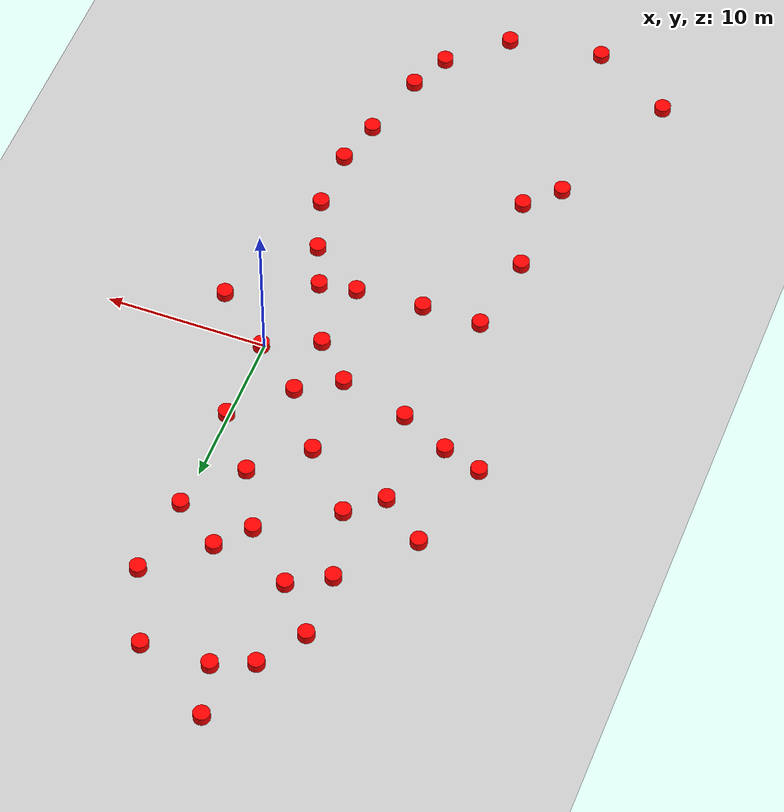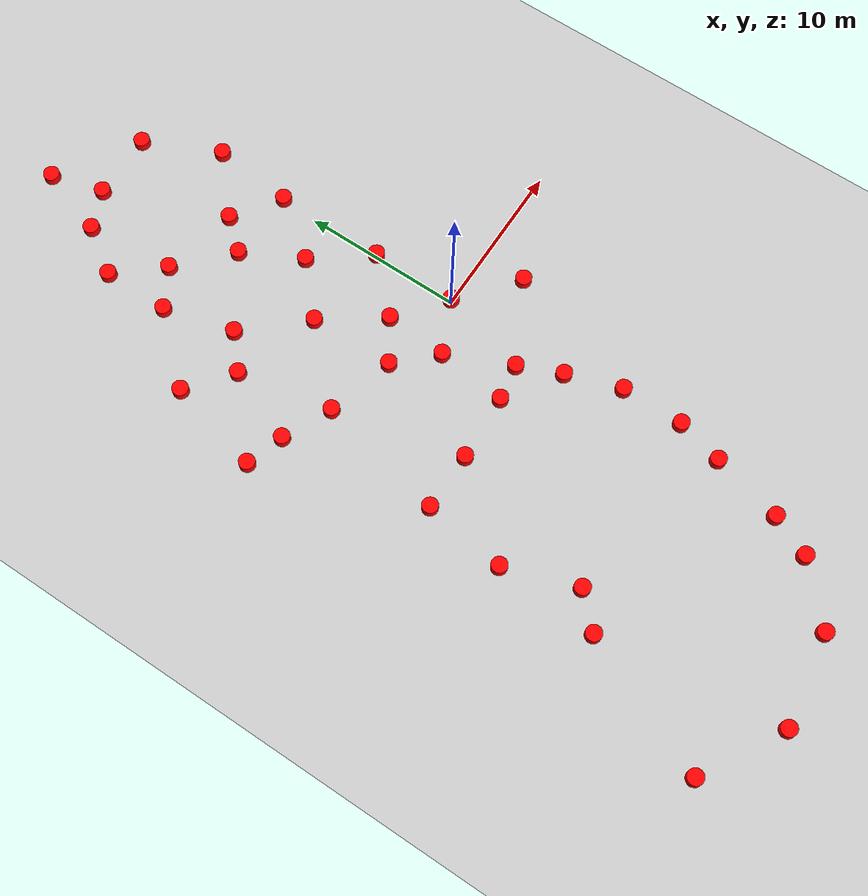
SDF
<sdf version="1.7">
 <world name="default">
  <light name="sun" type="directional">
   <pose>0 0 10 0 -0 0</pose>
   <diffuse>0.8 0.8 0.8 1</diffuse>
   <specular>0.2 0.2 0.2 1</specular>
   <attenuation>
    <range>1000</range>
    <constant>0.9</constant>
    <linear>0.01</linear>
    <quadratic>0.001</quadratic>
   </attenuation>
   <direction>-0.5 0.1 -0.9</direction>
   <spot><inner_angle>0</inner_angle><outer_angle>0</outer_angle><falloff>0</falloff></spot>
  </light>
  <model name="ground_plane">
   <static>1</static>
   <link name="link">
    <collision name="collision">
     <geometry><plane><normal>0 0 1</normal><size>100 100</size></plane></geometry>
     <surface><friction><ode><mu>100</mu><mu2>50</mu2></ode></friction></surface>
    </collision>
    <visual name="visual">
     <cast_shadows>0</cast_shadows>
     <geometry><plane><normal>0 0 1</normal><size>100 100</size></plane></geometry>
     <material>
      <script><uri>file://media/materials/scripts/gazebo.material</uri><name>Gazebo/Grey</name></script>
     </material>
    </visual>
   </link>
  </model>
  <gravity>0 0 -9.8</gravity>
  <magnetic_field>6e-06 2.3e-05 -4.2e-05</magnetic_field>
  <atmosphere type="adiabatic"/>
  <physics type="ode">
   <max_step_size>0.001</max_step_size>
   <real_time_factor>1</real_time_factor>
   <real_time_update_rate>1000</real_time_update_rate>
  </physics>
  <scene><ambient>0.4 0.4 0.4 1</ambient><background>0.7 0.7 0.7 1</background><shadows>1</shadows></scene>
  <spherical_coordinates>
   <surface_model>EARTH_WGS84</surface_model>
   <latitude_deg>0</latitude_deg>
   <longitude_deg>0</longitude_deg>
   <elevation>0</elevation>
   <heading_deg>0</heading_deg>
  </spherical_coordinates>
  <model name="prognocol">
   <link name="link_1">
    <inertial>
     <mass>1</mass>
     <inertia><ixx>0.145833</ixx><ixy>0</ixy><ixz>0</ixz><iyy>0.145833</iyy><iyz>0</iyz><izz>0.125</izz></inertia>
    </inertial>
    <pose>-0.052879 4.93849 0.5 0 -0 0</pose>
    <visual name="visual">
     <geometry><cylinder><radius>0.5</radius><length>1</length></cylinder></geometry>
     <material>
      <lighting>1</lighting>
      <script><uri>file://media/materials/scripts/gazebo.material</uri><name>Gazebo/Grey</name></script>
      <shader type="pixel"><normal_map>__default__</normal_map></shader>
      <ambient>1 0 0 0</ambient>
      <diffuse>0.7 0.7 0.7 1</diffuse>
      <specular>0.01 0.01 0.01 1</specular>
      <emissive>0 0 0 1</emissive>
     </material>
    </visual>
    <collision name="collision">
     <geometry><cylinder><radius>0.0005</radius><length>1e-05</length></cylinder></geometry>
     <surface>
      <friction>
       <ode><mu>1</mu><mu2>1</mu2><fdir1>0 0 0</fdir1><slip1>0</slip1><slip2>0</slip2></ode>
       <torsional>
        <coefficient>1</coefficient>
        <patch_radius>0</patch_radius>
        <surface_radius>0</surface_radius>
        <use_patch_radius>1</use_patch_radius>
        <ode><slip>0</slip></ode>
       </torsional>
      </friction>
      <bounce><restitution_coefficient>0</restitution_coefficient><threshold>1e+06</threshold></bounce>
      <contact>
       <collide_without_contact>0</collide_without_contact>
       <collide_without_contact_bitmask>1</collide_without_contact_bitmask>
       <collide_bitmask>1</collide_bitmask>
       <ode>
        <soft_cfm>0</soft_cfm>
        <soft_erp>0.2</soft_erp>
        <kp>1e+13</kp>
        <kd>1</kd>
        <max_vel>0.01</max_vel>
        <min_depth>0</min_depth>
       </ode>
       <bullet>
        <split_impulse>1</split_impulse>
        <split_impulse_penetration_threshold>-0.01</split_impulse_penetration_threshold>
        <soft_cfm>0</soft_cfm>
        <soft_erp>0.2</soft_erp>
        <kp>1e+13</kp>
        <kd>1</kd>
       </bullet>
      </contact>
     </surface>
    </collision>
   </link>
   <link name="link_1_clone">
    <inertial>
     <mass>1</mass>
     <inertia><ixx>0.145833</ixx><ixy>0</ixy><ixz>0</ixz><iyy>0.145833</iyy><iyz>0</iyz><izz>0.125</izz></inertia>
    </inertial>
    <pose>2.98374 2.57243 0.5 0 -0 0</pose>
    <visual name="visual">
     <geometry><cylinder><radius>0.5</radius><length>1</length></cylinder></geometry>
     <material>
      <lighting>1</lighting>
      <script><uri>file://media/materials/scripts/gazebo.material</uri><name>Gazebo/Grey</name></script>
      <shader type="pixel"><normal_map>__default__</normal_map></shader>
      <ambient>1 0 0 0</ambient>
      <diffuse>0.7 0.7 0.7 1</diffuse>
      <specular>0.01 0.01 0.01 1</specular>
      <emissive>0 0 0 1</emissive>
     </material>
    </visual>
    <collision name="collision">
     <geometry><cylinder><radius>0.0005</radius><length>1e-05</length></cylinder></geometry>
     <surface>
      <friction>
       <ode><mu>1</mu><mu2>1</mu2><fdir1>0 0 0</fdir1><slip1>0</slip1><slip2>0</slip2></ode>
       <torsional>
        <coefficient>1</coefficient>
        <patch_radius>0</patch_radius>
        <surface_radius>0</surface_radius>
        <use_patch_radius>1</use_patch_radius>
        <ode><slip>0</slip></ode>
       </torsional>
      </friction>
      <bounce><restitution_coefficient>0</restitution_coefficient><threshold>1e+06</threshold></bounce>
      <contact>
       <collide_without_contact>0</collide_without_contact>
       <collide_without_contact_bitmask>1</collide_without_contact_bitmask>
       <collide_bitmask>1</collide_bitmask>
       <ode>
        <soft_cfm>0</soft_cfm>
        <soft_erp>0.2</soft_erp>
        <kp>1e+13</kp>
        <kd>1</kd>
        <max_vel>0.01</max_vel>
        <min_depth>0</min_depth>
       </ode>
       <bullet>
        <split_impulse>1</split_impulse>
        <split_impulse_penetration_threshold>-0.01</split_impulse_penetration_threshold>
        <soft_cfm>0</soft_cfm>
        <soft_erp>0.2</soft_erp>
        <kp>1e+13</kp>
        <kd>1</kd>
       </bullet>
      </contact>
     </surface>
    </collision>
   </link>
   <link name="link_1_clone_0">
    <inertial>
     <mass>1</mass>
     <inertia><ixx>0.145833</ixx><ixy>0</ixy><ixz>0</ixz><iyy>0.145833</iyy><iyz>0</iyz><izz>0.125</izz></inertia>
    </inertial>
    <pose>6.50341 -0.320015 0.5 0 -0 0</pose>
    <visual name="visual">
     <geometry><cylinder><radius>0.5</radius><length>1</length></cylinder></geometry>
     <material>
      <lighting>1</lighting>
      <script><uri>file://media/materials/scripts/gazebo.material</uri><name>Gazebo/Grey</name></script>
      <shader type="pixel"><normal_map>__default__</normal_map></shader>
      <ambient>1 0 0 0</ambient>
      <diffuse>0.7 0.7 0.7 1</diffuse>
      <specular>0.01 0.01 0.01 1</specular>
      <emissive>0 0 0 1</emissive>
     </material>
    </visual>
    <collision name="collision">
     <geometry><cylinder><radius>0.0005</radius><length>1e-05</length></cylinder></geometry>
     <surface>
      <friction>
       <ode><mu>1</mu><mu2>1</mu2><fdir1>0 0 0</fdir1><slip1>0</slip1><slip2>0</slip2></ode>
       <torsional>
        <coefficient>1</coefficient>
        <patch_radius>0</patch_radius>
        <surface_radius>0</surface_radius>
        <use_patch_radius>1</use_patch_radius>
        <ode><slip>0</slip></ode>
       </torsional>
      </friction>
      <bounce><restitution_coefficient>0</restitution_coefficient><threshold>1e+06</threshold></bounce>
      <contact>
       <collide_without_contact>0</collide_without_contact>
       <collide_without_contact_bitmask>1</collide_without_contact_bitmask>
       <collide_bitmask>1</collide_bitmask>
       <ode>
        <soft_cfm>0</soft_cfm>
        <soft_erp>0.2</soft_erp>
        <kp>1e+13</kp>
        <kd>1</kd>
        <max_vel>0.01</max_vel>
        <min_depth>0</min_depth>
       </ode>
       <bullet>
        <split_impulse>1</split_impulse>
        <split_impulse_penetration_threshold>-0.01</split_impulse_penetration_threshold>
        <soft_cfm>0</soft_cfm>
        <soft_erp>0.2</soft_erp>
        <kp>1e+13</kp>
        <kd>1</kd>
       </bullet>
      </contact>
     </surface>
    </collision>
   </link>
   <link name="link_1_clone_1">
    <inertial>
     <mass>1</mass>
     <inertia><ixx>0.145833</ixx><ixy>0</ixy><ixz>0</ixz><iyy>0.145833</iyy><iyz>0</iyz><izz>0.125</izz></inertia>
    </inertial>
    <pose>2.98374 7.97688 0.5 0 -0 0</pose>
    <visual name="visual">
     <geometry><cylinder><radius>0.5</radius><length>1</length></cylinder></geometry>
     <material>
      <lighting>1</lighting>
      <script><uri>file://media/materials/scripts/gazebo.material</uri><name>Gazebo/Grey</name></script>
      <shader type="pixel"><normal_map>__default__</normal_map></shader>
      <ambient>1 0 0 0</ambient>
      <diffuse>0.7 0.7 0.7 1</diffuse>
      <specular>0.01 0.01 0.01 1</specular>
      <emissive>0 0 0 1</emissive>
     </material>
    </visual>
    <collision name="collision">
     <geometry><cylinder><radius>0.0005</radius><length>1e-05</length></cylinder></geometry>
     <surface>
      <friction>
       <ode><mu>1</mu><mu2>1</mu2><fdir1>0 0 0</fdir1><slip1>0</slip1><slip2>0</slip2></ode>
       <torsional>
        <coefficient>1</coefficient>
        <patch_radius>0</patch_radius>
        <surface_radius>0</surface_radius>
        <use_patch_radius>1</use_patch_radius>
        <ode><slip>0</slip></ode>
       </torsional>
      </friction>
      <bounce><restitution_coefficient>0</restitution_coefficient><threshold>1e+06</threshold></bounce>
      <contact>
       <collide_without_contact>0</collide_without_contact>
       <collide_without_contact_bitmask>1</collide_without_contact_bitmask>
       <collide_bitmask>1</collide_bitmask>
       <ode>
        <soft_cfm>0</soft_cfm>
        <soft_erp>0.2</soft_erp>
        <kp>1e+13</kp>
        <kd>1</kd>
        <max_vel>0.01</max_vel>
        <min_depth>0</min_depth>
       </ode>
       <bullet>
        <split_impulse>1</split_impulse>
        <split_impulse_penetration_threshold>-0.01</split_impulse_penetration_threshold>
        <soft_cfm>0</soft_cfm>
        <soft_erp>0.2</soft_erp>
        <kp>1e+13</kp>
        <kd>1</kd>
       </bullet>
      </contact>
     </surface>
    </collision>
   </link>
   <link name="link_1_clone_10">
    <inertial>
     <mass>1</mass>
     <inertia><ixx>0.145833</ixx><ixy>0</ixy><ixz>0</ixz><iyy>0.145833</iyy><iyz>0</iyz><izz>0.125</izz></inertia>
    </inertial>
    <pose>-7.07233 16.5239 0.5 0 -0 0</pose>
    <visual name="visual">
     <geometry><cylinder><radius>0.5</radius><length>1</length></cylinder></geometry>
     <material>
      <lighting>1</lighting>
      <script><uri>file://media/materials/scripts/gazebo.material</uri><name>Gazebo/Grey</name></script>
      <shader type="pixel"><normal_map>__default__</normal_map></shader>
      <ambient>1 0 0 0</ambient>
      <diffuse>0.7 0.7 0.7 1</diffuse>
      <specular>0.01 0.01 0.01 1</specular>
      <emissive>0 0 0 1</emissive>
     </material>
    </visual>
    <collision name="collision">
     <geometry><cylinder><radius>0.0005</radius><length>1e-05</length></cylinder></geometry>
     <surface>
      <friction>
       <ode><mu>1</mu><mu2>1</mu2><fdir1>0 0 0</fdir1><slip1>0</slip1><slip2>0</slip2></ode>
       <torsional>
        <coefficient>1</coefficient>
        <patch_radius>0</patch_radius>
        <surface_radius>0</surface_radius>
        <use_patch_radius>1</use_patch_radius>
        <ode><slip>0</slip></ode>
       </torsional>
      </friction>
      <bounce><restitution_coefficient>0</restitution_coefficient><threshold>1e+06</threshold></bounce>
      <contact>
       <collide_without_contact>0</collide_without_contact>
       <collide_without_contact_bitmask>1</collide_without_contact_bitmask>
       <collide_bitmask>1</collide_bitmask>
       <ode>
        <soft_cfm>0</soft_cfm>
        <soft_erp>0.2</soft_erp>
        <kp>1e+13</kp>
        <kd>1</kd>
        <max_vel>0.01</max_vel>
        <min_depth>0</min_depth>
       </ode>
       <bullet>
        <split_impulse>1</split_impulse>
        <split_impulse_penetration_threshold>-0.01</split_impulse_penetration_threshold>
        <soft_cfm>0</soft_cfm>
        <soft_erp>0.2</soft_erp>
        <kp>1e+13</kp>
        <kd>1</kd>
       </bullet>
      </contact>
     </surface>
    </collision>
   </link>
   <link name="link_1_clone_11">
    <inertial>
     <mass>1</mass>
     <inertia><ixx>0.145833</ixx><ixy>0</ixy><ixz>0</ixz><iyy>0.145833</iyy><iyz>0</iyz><izz>0.125</izz></inertia>
    </inertial>
    <pose>0.092599 16.9013 0.5 0 -0 0</pose>
    <visual name="visual">
     <geometry><cylinder><radius>0.5</radius><length>1</length></cylinder></geometry>
     <material>
      <lighting>1</lighting>
      <script><uri>file://media/materials/scripts/gazebo.material</uri><name>Gazebo/Grey</name></script>
      <shader type="pixel"><normal_map>__default__</normal_map></shader>
      <ambient>1 0 0 0</ambient>
      <diffuse>0.7 0.7 0.7 1</diffuse>
      <specular>0.01 0.01 0.01 1</specular>
      <emissive>0 0 0 1</emissive>
     </material>
    </visual>
    <collision name="collision">
     <geometry><cylinder><radius>0.0005</radius><length>1e-05</length></cylinder></geometry>
     <surface>
      <friction>
       <ode><mu>1</mu><mu2>1</mu2><fdir1>0 0 0</fdir1><slip1>0</slip1><slip2>0</slip2></ode>
       <torsional>
        <coefficient>1</coefficient>
        <patch_radius>0</patch_radius>
        <surface_radius>0</surface_radius>
        <use_patch_radius>1</use_patch_radius>
        <ode><slip>0</slip></ode>
       </torsional>
      </friction>
      <bounce><restitution_coefficient>0</restitution_coefficient><threshold>1e+06</threshold></bounce>
      <contact>
       <collide_without_contact>0</collide_without_contact>
       <collide_without_contact_bitmask>1</collide_without_contact_bitmask>
       <collide_bitmask>1</collide_bitmask>
       <ode>
        <soft_cfm>0</soft_cfm>
        <soft_erp>0.2</soft_erp>
        <kp>1e+13</kp>
        <kd>1</kd>
        <max_vel>0.01</max_vel>
        <min_depth>0</min_depth>
       </ode>
       <bullet>
        <split_impulse>1</split_impulse>
        <split_impulse_penetration_threshold>-0.01</split_impulse_penetration_threshold>
        <soft_cfm>0</soft_cfm>
        <soft_erp>0.2</soft_erp>
        <kp>1e+13</kp>
        <kd>1</kd>
       </bullet>
      </contact>
     </surface>
    </collision>
   </link>
   <link name="link_1_clone_12">
    <inertial>
     <mass>1</mass>
     <inertia><ixx>0.145833</ixx><ixy>0</ixy><ixz>0</ixz><iyy>0.145833</iyy><iyz>0</iyz><izz>0.125</izz></inertia>
    </inertial>
    <pose>-1.5415 15.0157 0.5 0 -0 0</pose>
    <visual name="visual">
     <geometry><cylinder><radius>0.5</radius><length>1</length></cylinder></geometry>
     <material>
      <lighting>1</lighting>
      <script><uri>file://media/materials/scripts/gazebo.material</uri><name>Gazebo/Grey</name></script>
      <shader type="pixel"><normal_map>__default__</normal_map></shader>
      <ambient>1 0 0 0</ambient>
      <diffuse>0.7 0.7 0.7 1</diffuse>
      <specular>0.01 0.01 0.01 1</specular>
      <emissive>0 0 0 1</emissive>
     </material>
    </visual>
    <collision name="collision">
     <geometry><cylinder><radius>0.0005</radius><length>1e-05</length></cylinder></geometry>
     <surface>
      <friction>
       <ode><mu>1</mu><mu2>1</mu2><fdir1>0 0 0</fdir1><slip1>0</slip1><slip2>0</slip2></ode>
       <torsional>
        <coefficient>1</coefficient>
        <patch_radius>0</patch_radius>
        <surface_radius>0</surface_radius>
        <use_patch_radius>1</use_patch_radius>
        <ode><slip>0</slip></ode>
       </torsional>
      </friction>
      <bounce><restitution_coefficient>0</restitution_coefficient><threshold>1e+06</threshold></bounce>
      <contact>
       <collide_without_contact>0</collide_without_contact>
       <collide_without_contact_bitmask>1</collide_without_contact_bitmask>
       <collide_bitmask>1</collide_bitmask>
       <ode>
        <soft_cfm>0</soft_cfm>
        <soft_erp>0.2</soft_erp>
        <kp>1e+13</kp>
        <kd>1</kd>
        <max_vel>0.01</max_vel>
        <min_depth>0</min_depth>
       </ode>
       <bullet>
        <split_impulse>1</split_impulse>
        <split_impulse_penetration_threshold>-0.01</split_impulse_penetration_threshold>
        <soft_cfm>0</soft_cfm>
        <soft_erp>0.2</soft_erp>
        <kp>1e+13</kp>
        <kd>1</kd>
       </bullet>
      </contact>
     </surface>
    </collision>
   </link>
   <link name="link_1_clone_13">
    <inertial>
     <mass>1</mass>
     <inertia><ixx>0.145833</ixx><ixy>0</ixy><ixz>0</ixz><iyy>0.145833</iyy><iyz>0</iyz><izz>0.125</izz></inertia>
    </inertial>
    <pose>0.3438 11.3696 0.5 0 -0 0</pose>
    <visual name="visual">
     <geometry><cylinder><radius>0.5</radius><length>1</length></cylinder></geometry>
     <material>
      <lighting>1</lighting>
      <script><uri>file://media/materials/scripts/gazebo.material</uri><name>Gazebo/Grey</name></script>
      <shader type="pixel"><normal_map>__default__</normal_map></shader>
      <ambient>1 0 0 0</ambient>
      <diffuse>0.7 0.7 0.7 1</diffuse>
      <specular>0.01 0.01 0.01 1</specular>
      <emissive>0 0 0 1</emissive>
     </material>
    </visual>
    <collision name="collision">
     <geometry><cylinder><radius>0.0005</radius><length>1e-05</length></cylinder></geometry>
     <surface>
      <friction>
       <ode><mu>1</mu><mu2>1</mu2><fdir1>0 0 0</fdir1><slip1>0</slip1><slip2>0</slip2></ode>
       <torsional>
        <coefficient>1</coefficient>
        <patch_radius>0</patch_radius>
        <surface_radius>0</surface_radius>
        <use_patch_radius>1</use_patch_radius>
        <ode><slip>0</slip></ode>
       </torsional>
      </friction>
      <bounce><restitution_coefficient>0</restitution_coefficient><threshold>1e+06</threshold></bounce>
      <contact>
       <collide_without_contact>0</collide_without_contact>
       <collide_without_contact_bitmask>1</collide_without_contact_bitmask>
       <collide_bitmask>1</collide_bitmask>
       <ode>
        <soft_cfm>0</soft_cfm>
        <soft_erp>0.2</soft_erp>
        <kp>1e+13</kp>
        <kd>1</kd>
        <max_vel>0.01</max_vel>
        <min_depth>0</min_depth>
       </ode>
       <bullet>
        <split_impulse>1</split_impulse>
        <split_impulse_penetration_threshold>-0.01</split_impulse_penetration_threshold>
        <soft_cfm>0</soft_cfm>
        <soft_erp>0.2</soft_erp>
        <kp>1e+13</kp>
        <kd>1</kd>
       </bullet>
      </contact>
     </surface>
    </collision>
   </link>
   <link name="link_1_clone_14">
    <inertial>
     <mass>1</mass>
     <inertia><ixx>0.145833</ixx><ixy>0</ixy><ixz>0</ixz><iyy>0.145833</iyy><iyz>0</iyz><izz>0.125</izz></inertia>
    </inertial>
    <pose>-0.284722 1.06315 0.5 0 -0 0</pose>
    <visual name="visual">
     <geometry><cylinder><radius>0.5</radius><length>1</length></cylinder></geometry>
     <material>
      <lighting>1</lighting>
      <script><uri>file://media/materials/scripts/gazebo.material</uri><name>Gazebo/Grey</name></script>
      <shader type="pixel"><normal_map>__default__</normal_map></shader>
      <ambient>1 0 0 0</ambient>
      <diffuse>0.7 0.7 0.7 1</diffuse>
      <specular>0.01 0.01 0.01 1</specular>
      <emissive>0 0 0 1</emissive>
     </material>
    </visual>
    <collision name="collision">
     <geometry><cylinder><radius>0.0005</radius><length>1e-05</length></cylinder></geometry>
     <surface>
      <friction>
       <ode><mu>1</mu><mu2>1</mu2><fdir1>0 0 0</fdir1><slip1>0</slip1><slip2>0</slip2></ode>
       <torsional>
        <coefficient>1</coefficient>
        <patch_radius>0</patch_radius>
        <surface_radius>0</surface_radius>
        <use_patch_radius>1</use_patch_radius>
        <ode><slip>0</slip></ode>
       </torsional>
      </friction>
      <bounce><restitution_coefficient>0</restitution_coefficient><threshold>1e+06</threshold></bounce>
      <contact>
       <collide_without_contact>0</collide_without_contact>
       <collide_without_contact_bitmask>1</collide_without_contact_bitmask>
       <collide_bitmask>1</collide_bitmask>
       <ode>
        <soft_cfm>0</soft_cfm>
        <soft_erp>0.2</soft_erp>
        <kp>1e+13</kp>
        <kd>1</kd>
        <max_vel>0.01</max_vel>
        <min_depth>0</min_depth>
       </ode>
       <bullet>
        <split_impulse>1</split_impulse>
        <split_impulse_penetration_threshold>-0.01</split_impulse_penetration_threshold>
        <soft_cfm>0</soft_cfm>
        <soft_erp>0.2</soft_erp>
        <kp>1e+13</kp>
        <kd>1</kd>
       </bullet>
      </contact>
     </surface>
    </collision>
   </link>
   <link name="link_1_clone_15">
    <inertial>
     <mass>1</mass>
     <inertia><ixx>0.145833</ixx><ixy>0</ixy><ixz>0</ixz><iyy>0.145833</iyy><iyz>0</iyz><izz>0.125</izz></inertia>
    </inertial>
    <pose>-2.67269 8.6054 0.5 0 -0 0</pose>
    <visual name="visual">
     <geometry><cylinder><radius>0.5</radius><length>1</length></cylinder></geometry>
     <material>
      <lighting>1</lighting>
      <script><uri>file://media/materials/scripts/gazebo.material</uri><name>Gazebo/Grey</name></script>
      <shader type="pixel"><normal_map>__default__</normal_map></shader>
      <ambient>1 0 0 0</ambient>
      <diffuse>0.7 0.7 0.7 1</diffuse>
      <specular>0.01 0.01 0.01 1</specular>
      <emissive>0 0 0 1</emissive>
     </material>
    </visual>
    <collision name="collision">
     <geometry><cylinder><radius>0.0005</radius><length>1e-05</length></cylinder></geometry>
     <surface>
      <friction>
       <ode><mu>1</mu><mu2>1</mu2><fdir1>0 0 0</fdir1><slip1>0</slip1><slip2>0</slip2></ode>
       <torsional>
        <coefficient>1</coefficient>
        <patch_radius>0</patch_radius>
        <surface_radius>0</surface_radius>
        <use_patch_radius>1</use_patch_radius>
        <ode><slip>0</slip></ode>
       </torsional>
      </friction>
      <bounce><restitution_coefficient>0</restitution_coefficient><threshold>1e+06</threshold></bounce>
      <contact>
       <collide_without_contact>0</collide_without_contact>
       <collide_without_contact_bitmask>1</collide_without_contact_bitmask>
       <collide_bitmask>1</collide_bitmask>
       <ode>
        <soft_cfm>0</soft_cfm>
        <soft_erp>0.2</soft_erp>
        <kp>1e+13</kp>
        <kd>1</kd>
        <max_vel>0.01</max_vel>
        <min_depth>0</min_depth>
       </ode>
       <bullet>
        <split_impulse>1</split_impulse>
        <split_impulse_penetration_threshold>-0.01</split_impulse_penetration_threshold>
        <soft_cfm>0</soft_cfm>
        <soft_erp>0.2</soft_erp>
        <kp>1e+13</kp>
        <kd>1</kd>
       </bullet>
      </contact>
     </surface>
    </collision>
   </link>
   <link name="link_1_clone_16">
    <inertial>
     <mass>1</mass>
     <inertia><ixx>0.145833</ixx><ixy>0</ixy><ixz>0</ixz><iyy>0.145833</iyy><iyz>0</iyz><izz>0.125</izz></inertia>
    </inertial>
    <pose>-2.54709 3.32603 0.5 0 -0 0</pose>
    <visual name="visual">
     <geometry><cylinder><radius>0.5</radius><length>1</length></cylinder></geometry>
     <material>
      <lighting>1</lighting>
      <script><uri>file://media/materials/scripts/gazebo.material</uri><name>Gazebo/Grey</name></script>
      <shader type="pixel"><normal_map>__default__</normal_map></shader>
      <ambient>1 0 0 0</ambient>
      <diffuse>0.7 0.7 0.7 1</diffuse>
      <specular>0.01 0.01 0.01 1</specular>
      <emissive>0 0 0 1</emissive>
     </material>
    </visual>
    <collision name="collision">
     <geometry><cylinder><radius>0.0005</radius><length>1e-05</length></cylinder></geometry>
     <surface>
      <friction>
       <ode><mu>1</mu><mu2>1</mu2><fdir1>0 0 0</fdir1><slip1>0</slip1><slip2>0</slip2></ode>
       <torsional>
        <coefficient>1</coefficient>
        <patch_radius>0</patch_radius>
        <surface_radius>0</surface_radius>
        <use_patch_radius>1</use_patch_radius>
        <ode><slip>0</slip></ode>
       </torsional>
      </friction>
      <bounce><restitution_coefficient>0</restitution_coefficient><threshold>1e+06</threshold></bounce>
      <contact>
       <collide_without_contact>0</collide_without_contact>
       <collide_without_contact_bitmask>1</collide_without_contact_bitmask>
       <collide_bitmask>1</collide_bitmask>
       <ode>
        <soft_cfm>0</soft_cfm>
        <soft_erp>0.2</soft_erp>
        <kp>1e+13</kp>
        <kd>1</kd>
        <max_vel>0.01</max_vel>
        <min_depth>0</min_depth>
       </ode>
       <bullet>
        <split_impulse>1</split_impulse>
        <split_impulse_penetration_threshold>-0.01</split_impulse_penetration_threshold>
        <soft_cfm>0</soft_cfm>
        <soft_erp>0.2</soft_erp>
        <kp>1e+13</kp>
        <kd>1</kd>
       </bullet>
      </contact>
     </surface>
    </collision>
   </link>
   <link name="link_1_clone_17">
    <inertial>
     <mass>1</mass>
     <inertia><ixx>0.145833</ixx><ixy>0</ixy><ixz>0</ixz><iyy>0.145833</iyy><iyz>0</iyz><izz>0.125</izz></inertia>
    </inertial>
    <pose>-6.82061 4.45695 0.5 0 -0 0</pose>
    <visual name="visual">
     <geometry><cylinder><radius>0.5</radius><length>1</length></cylinder></geometry>
     <material>
      <lighting>1</lighting>
      <script><uri>file://media/materials/scripts/gazebo.material</uri><name>Gazebo/Grey</name></script>
      <shader type="pixel"><normal_map>__default__</normal_map></shader>
      <ambient>1 0 0 0</ambient>
      <diffuse>0.7 0.7 0.7 1</diffuse>
      <specular>0.01 0.01 0.01 1</specular>
      <emissive>0 0 0 1</emissive>
     </material>
    </visual>
    <collision name="collision">
     <geometry><cylinder><radius>0.0005</radius><length>1e-05</length></cylinder></geometry>
     <surface>
      <friction>
       <ode><mu>1</mu><mu2>1</mu2><fdir1>0 0 0</fdir1><slip1>0</slip1><slip2>0</slip2></ode>
       <torsional>
        <coefficient>1</coefficient>
        <patch_radius>0</patch_radius>
        <surface_radius>0</surface_radius>
        <use_patch_radius>1</use_patch_radius>
        <ode><slip>0</slip></ode>
       </torsional>
      </friction>
      <bounce><restitution_coefficient>0</restitution_coefficient><threshold>1e+06</threshold></bounce>
      <contact>
       <collide_without_contact>0</collide_without_contact>
       <collide_without_contact_bitmask>1</collide_without_contact_bitmask>
       <collide_bitmask>1</collide_bitmask>
       <ode>
        <soft_cfm>0</soft_cfm>
        <soft_erp>0.2</soft_erp>
        <kp>1e+13</kp>
        <kd>1</kd>
        <max_vel>0.01</max_vel>
        <min_depth>0</min_depth>
       </ode>
       <bullet>
        <split_impulse>1</split_impulse>
        <split_impulse_penetration_threshold>-0.01</split_impulse_penetration_threshold>
        <soft_cfm>0</soft_cfm>
        <soft_erp>0.2</soft_erp>
        <kp>1e+13</kp>
        <kd>1</kd>
       </bullet>
      </contact>
     </surface>
    </collision>
   </link>
   <link name="link_1_clone_18">
    <inertial>
     <mass>1</mass>
     <inertia><ixx>0.145833</ixx><ixy>0</ixy><ixz>0</ixz><iyy>0.145833</iyy><iyz>0</iyz><izz>0.125</izz></inertia>
    </inertial>
    <pose>-9.83736 5.84012 0.5 0 -0 0</pose>
    <visual name="visual">
     <geometry><cylinder><radius>0.5</radius><length>1</length></cylinder></geometry>
     <material>
      <lighting>1</lighting>
      <script><uri>file://media/materials/scripts/gazebo.material</uri><name>Gazebo/Grey</name></script>
      <shader type="pixel"><normal_map>__default__</normal_map></shader>
      <ambient>1 0 0 0</ambient>
      <diffuse>0.7 0.7 0.7 1</diffuse>
      <specular>0.01 0.01 0.01 1</specular>
      <emissive>0 0 0 1</emissive>
     </material>
    </visual>
    <collision name="collision">
     <geometry><cylinder><radius>0.0005</radius><length>1e-05</length></cylinder></geometry>
     <surface>
      <friction>
       <ode><mu>1</mu><mu2>1</mu2><fdir1>0 0 0</fdir1><slip1>0</slip1><slip2>0</slip2></ode>
       <torsional>
        <coefficient>1</coefficient>
        <patch_radius>0</patch_radius>
        <surface_radius>0</surface_radius>
        <use_patch_radius>1</use_patch_radius>
        <ode><slip>0</slip></ode>
       </torsional>
      </friction>
      <bounce><restitution_coefficient>0</restitution_coefficient><threshold>1e+06</threshold></bounce>
      <contact>
       <collide_without_contact>0</collide_without_contact>
       <collide_without_contact_bitmask>1</collide_without_contact_bitmask>
       <collide_bitmask>1</collide_bitmask>
       <ode>
        <soft_cfm>0</soft_cfm>
        <soft_erp>0.2</soft_erp>
        <kp>1e+13</kp>
        <kd>1</kd>
        <max_vel>0.01</max_vel>
        <min_depth>0</min_depth>
       </ode>
       <bullet>
        <split_impulse>1</split_impulse>
        <split_impulse_penetration_threshold>-0.01</split_impulse_penetration_threshold>
        <soft_cfm>0</soft_cfm>
        <soft_erp>0.2</soft_erp>
        <kp>1e+13</kp>
        <kd>1</kd>
       </bullet>
      </contact>
     </surface>
    </collision>
   </link>
   <link name="link_1_clone_19">
    <inertial>
     <mass>1</mass>
     <inertia><ixx>0.145833</ixx><ixy>0</ixy><ixz>0</ixz><iyy>0.145833</iyy><iyz>0</iyz><izz>0.125</izz></inertia>
    </inertial>
    <pose>-12.2258 6.59372 0.5 0 -0 0</pose>
    <visual name="visual">
     <geometry><cylinder><radius>0.5</radius><length>1</length></cylinder></geometry>
     <material>
      <lighting>1</lighting>
      <script><uri>file://media/materials/scripts/gazebo.material</uri><name>Gazebo/Grey</name></script>
      <shader type="pixel"><normal_map>__default__</normal_map></shader>
      <ambient>1 0 0 0</ambient>
      <diffuse>0.7 0.7 0.7 1</diffuse>
      <specular>0.01 0.01 0.01 1</specular>
      <emissive>0 0 0 1</emissive>
     </material>
    </visual>
    <collision name="collision">
     <geometry><cylinder><radius>0.0005</radius><length>1e-05</length></cylinder></geometry>
     <surface>
      <friction>
       <ode><mu>1</mu><mu2>1</mu2><fdir1>0 0 0</fdir1><slip1>0</slip1><slip2>0</slip2></ode>
       <torsional>
        <coefficient>1</coefficient>
        <patch_radius>0</patch_radius>
        <surface_radius>0</surface_radius>
        <use_patch_radius>1</use_patch_radius>
        <ode><slip>0</slip></ode>
       </torsional>
      </friction>
      <bounce><restitution_coefficient>0</restitution_coefficient><threshold>1e+06</threshold></bounce>
      <contact>
       <collide_without_contact>0</collide_without_contact>
       <collide_without_contact_bitmask>1</collide_without_contact_bitmask>
       <collide_bitmask>1</collide_bitmask>
       <ode>
        <soft_cfm>0</soft_cfm>
        <soft_erp>0.2</soft_erp>
        <kp>1e+13</kp>
        <kd>1</kd>
        <max_vel>0.01</max_vel>
        <min_depth>0</min_depth>
       </ode>
       <bullet>
        <split_impulse>1</split_impulse>
        <split_impulse_penetration_threshold>-0.01</split_impulse_penetration_threshold>
        <soft_cfm>0</soft_cfm>
        <soft_erp>0.2</soft_erp>
        <kp>1e+13</kp>
        <kd>1</kd>
       </bullet>
      </contact>
     </surface>
    </collision>
   </link>
   <link name="link_1_clone_2">
    <inertial>
     <mass>1</mass>
     <inertia><ixx>0.145833</ixx><ixy>0</ixy><ixz>0</ixz><iyy>0.145833</iyy><iyz>0</iyz><izz>0.125</izz></inertia>
    </inertial>
    <pose>2.98374 14.8896 0.5 0 -0 0</pose>
    <visual name="visual">
     <geometry><cylinder><radius>0.5</radius><length>1</length></cylinder></geometry>
     <material>
      <lighting>1</lighting>
      <script><uri>file://media/materials/scripts/gazebo.material</uri><name>Gazebo/Grey</name></script>
      <shader type="pixel"><normal_map>__default__</normal_map></shader>
      <ambient>1 0 0 0</ambient>
      <diffuse>0.7 0.7 0.7 1</diffuse>
      <specular>0.01 0.01 0.01 1</specular>
      <emissive>0 0 0 1</emissive>
     </material>
    </visual>
    <collision name="collision">
     <geometry><cylinder><radius>0.0005</radius><length>1e-05</length></cylinder></geometry>
     <surface>
      <friction>
       <ode><mu>1</mu><mu2>1</mu2><fdir1>0 0 0</fdir1><slip1>0</slip1><slip2>0</slip2></ode>
       <torsional>
        <coefficient>1</coefficient>
        <patch_radius>0</patch_radius>
        <surface_radius>0</surface_radius>
        <use_patch_radius>1</use_patch_radius>
        <ode><slip>0</slip></ode>
       </torsional>
      </friction>
      <bounce><restitution_coefficient>0</restitution_coefficient><threshold>1e+06</threshold></bounce>
      <contact>
       <collide_without_contact>0</collide_without_contact>
       <collide_without_contact_bitmask>1</collide_without_contact_bitmask>
       <collide_bitmask>1</collide_bitmask>
       <ode>
        <soft_cfm>0</soft_cfm>
        <soft_erp>0.2</soft_erp>
        <kp>1e+13</kp>
        <kd>1</kd>
        <max_vel>0.01</max_vel>
        <min_depth>0</min_depth>
       </ode>
       <bullet>
        <split_impulse>1</split_impulse>
        <split_impulse_penetration_threshold>-0.01</split_impulse_penetration_threshold>
        <soft_cfm>0</soft_cfm>
        <soft_erp>0.2</soft_erp>
        <kp>1e+13</kp>
        <kd>1</kd>
       </bullet>
      </contact>
     </surface>
    </collision>
   </link>
   <link name="link_1_clone_20">
    <inertial>
     <mass>1</mass>
     <inertia><ixx>0.145833</ixx><ixy>0</ixy><ixz>0</ixz><iyy>0.145833</iyy><iyz>0</iyz><izz>0.125</izz></inertia>
    </inertial>
    <pose>-5.94063 12.1253 0.5 0 -0 0</pose>
    <visual name="visual">
     <geometry><cylinder><radius>0.5</radius><length>1</length></cylinder></geometry>
     <material>
      <lighting>1</lighting>
      <script><uri>file://media/materials/scripts/gazebo.material</uri><name>Gazebo/Grey</name></script>
      <shader type="pixel"><normal_map>__default__</normal_map></shader>
      <ambient>1 0 0 0</ambient>
      <diffuse>0.7 0.7 0.7 1</diffuse>
      <specular>0.01 0.01 0.01 1</specular>
      <emissive>0 0 0 1</emissive>
     </material>
    </visual>
    <collision name="collision">
     <geometry><cylinder><radius>0.0005</radius><length>1e-05</length></cylinder></geometry>
     <surface>
      <friction>
       <ode><mu>1</mu><mu2>1</mu2><fdir1>0 0 0</fdir1><slip1>0</slip1><slip2>0</slip2></ode>
       <torsional>
        <coefficient>1</coefficient>
        <patch_radius>0</patch_radius>
        <surface_radius>0</surface_radius>
        <use_patch_radius>1</use_patch_radius>
        <ode><slip>0</slip></ode>
       </torsional>
      </friction>
      <bounce><restitution_coefficient>0</restitution_coefficient><threshold>1e+06</threshold></bounce>
      <contact>
       <collide_without_contact>0</collide_without_contact>
       <collide_without_contact_bitmask>1</collide_without_contact_bitmask>
       <collide_bitmask>1</collide_bitmask>
       <ode>
        <soft_cfm>0</soft_cfm>
        <soft_erp>0.2</soft_erp>
        <kp>1e+13</kp>
        <kd>1</kd>
        <max_vel>0.01</max_vel>
        <min_depth>0</min_depth>
       </ode>
       <bullet>
        <split_impulse>1</split_impulse>
        <split_impulse_penetration_threshold>-0.01</split_impulse_penetration_threshold>
        <soft_cfm>0</soft_cfm>
        <soft_erp>0.2</soft_erp>
        <kp>1e+13</kp>
        <kd>1</kd>
       </bullet>
      </contact>
     </surface>
    </collision>
   </link>
   <link name="link_1_clone_21">
    <inertial>
     <mass>1</mass>
     <inertia><ixx>0.145833</ixx><ixy>0</ixy><ixz>0</ixz><iyy>0.145833</iyy><iyz>0</iyz><izz>0.125</izz></inertia>
    </inertial>
    <pose>-7.95206 10.3648 0.5 0 -0 0</pose>
    <visual name="visual">
     <geometry><cylinder><radius>0.5</radius><length>1</length></cylinder></geometry>
     <material>
      <lighting>1</lighting>
      <script><uri>file://media/materials/scripts/gazebo.material</uri><name>Gazebo/Grey</name></script>
      <shader type="pixel"><normal_map>__default__</normal_map></shader>
      <ambient>1 0 0 0</ambient>
      <diffuse>0.7 0.7 0.7 1</diffuse>
      <specular>0.01 0.01 0.01 1</specular>
      <emissive>0 0 0 1</emissive>
     </material>
    </visual>
    <collision name="collision">
     <geometry><cylinder><radius>0.0005</radius><length>1e-05</length></cylinder></geometry>
     <surface>
      <friction>
       <ode><mu>1</mu><mu2>1</mu2><fdir1>0 0 0</fdir1><slip1>0</slip1><slip2>0</slip2></ode>
       <torsional>
        <coefficient>1</coefficient>
        <patch_radius>0</patch_radius>
        <surface_radius>0</surface_radius>
        <use_patch_radius>1</use_patch_radius>
        <ode><slip>0</slip></ode>
       </torsional>
      </friction>
      <bounce><restitution_coefficient>0</restitution_coefficient><threshold>1e+06</threshold></bounce>
      <contact>
       <collide_without_contact>0</collide_without_contact>
       <collide_without_contact_bitmask>1</collide_without_contact_bitmask>
       <collide_bitmask>1</collide_bitmask>
       <ode>
        <soft_cfm>0</soft_cfm>
        <soft_erp>0.2</soft_erp>
        <kp>1e+13</kp>
        <kd>1</kd>
        <max_vel>0.01</max_vel>
        <min_depth>0</min_depth>
       </ode>
       <bullet>
        <split_impulse>1</split_impulse>
        <split_impulse_penetration_threshold>-0.01</split_impulse_penetration_threshold>
        <soft_cfm>0</soft_cfm>
        <soft_erp>0.2</soft_erp>
        <kp>1e+13</kp>
        <kd>1</kd>
       </bullet>
      </contact>
     </surface>
    </collision>
   </link>
   <link name="link_1_clone_22">
    <inertial>
     <mass>1</mass>
     <inertia><ixx>0.145833</ixx><ixy>0</ixy><ixz>0</ixz><iyy>0.145833</iyy><iyz>0</iyz><izz>0.125</izz></inertia>
    </inertial>
    <pose>-10.7173 12.5016 0.5 0 -0 0</pose>
    <visual name="visual">
     <geometry><cylinder><radius>0.5</radius><length>1</length></cylinder></geometry>
     <material>
      <lighting>1</lighting>
      <script><uri>file://media/materials/scripts/gazebo.material</uri><name>Gazebo/Grey</name></script>
      <shader type="pixel"><normal_map>__default__</normal_map></shader>
      <ambient>1 0 0 0</ambient>
      <diffuse>0.7 0.7 0.7 1</diffuse>
      <specular>0.01 0.01 0.01 1</specular>
      <emissive>0 0 0 1</emissive>
     </material>
    </visual>
    <collision name="collision">
     <geometry><cylinder><radius>0.0005</radius><length>1e-05</length></cylinder></geometry>
     <surface>
      <friction>
       <ode><mu>1</mu><mu2>1</mu2><fdir1>0 0 0</fdir1><slip1>0</slip1><slip2>0</slip2></ode>
       <torsional>
        <coefficient>1</coefficient>
        <patch_radius>0</patch_radius>
        <surface_radius>0</surface_radius>
        <use_patch_radius>1</use_patch_radius>
        <ode><slip>0</slip></ode>
       </torsional>
      </friction>
      <bounce><restitution_coefficient>0</restitution_coefficient><threshold>1e+06</threshold></bounce>
      <contact>
       <collide_without_contact>0</collide_without_contact>
       <collide_without_contact_bitmask>1</collide_without_contact_bitmask>
       <collide_bitmask>1</collide_bitmask>
       <ode>
        <soft_cfm>0</soft_cfm>
        <soft_erp>0.2</soft_erp>
        <kp>1e+13</kp>
        <kd>1</kd>
        <max_vel>0.01</max_vel>
        <min_depth>0</min_depth>
       </ode>
       <bullet>
        <split_impulse>1</split_impulse>
        <split_impulse_penetration_threshold>-0.01</split_impulse_penetration_threshold>
        <soft_cfm>0</soft_cfm>
        <soft_erp>0.2</soft_erp>
        <kp>1e+13</kp>
        <kd>1</kd>
       </bullet>
      </contact>
     </surface>
    </collision>
   </link>
   <link name="link_1_clone_23">
    <inertial>
     <mass>1</mass>
     <inertia><ixx>0.145833</ixx><ixy>0</ixy><ixz>0</ixz><iyy>0.145833</iyy><iyz>0</iyz><izz>0.125</izz></inertia>
    </inertial>
    <pose>-0.787382 -3.33546 0.5 0 -0 0</pose>
    <visual name="visual">
     <geometry><cylinder><radius>0.5</radius><length>1</length></cylinder></geometry>
     <material>
      <lighting>1</lighting>
      <script><uri>file://media/materials/scripts/gazebo.material</uri><name>Gazebo/Grey</name></script>
      <shader type="pixel"><normal_map>__default__</normal_map></shader>
      <ambient>1 0 0 0</ambient>
      <diffuse>0.7 0.7 0.7 1</diffuse>
      <specular>0.01 0.01 0.01 1</specular>
      <emissive>0 0 0 1</emissive>
     </material>
    </visual>
    <collision name="collision">
     <geometry><cylinder><radius>0.0005</radius><length>1e-05</length></cylinder></geometry>
     <surface>
      <friction>
       <ode><mu>1</mu><mu2>1</mu2><fdir1>0 0 0</fdir1><slip1>0</slip1><slip2>0</slip2></ode>
       <torsional>
        <coefficient>1</coefficient>
        <patch_radius>0</patch_radius>
        <surface_radius>0</surface_radius>
        <use_patch_radius>1</use_patch_radius>
        <ode><slip>0</slip></ode>
       </torsional>
      </friction>
      <bounce><restitution_coefficient>0</restitution_coefficient><threshold>1e+06</threshold></bounce>
      <contact>
       <collide_without_contact>0</collide_without_contact>
       <collide_without_contact_bitmask>1</collide_without_contact_bitmask>
       <collide_bitmask>1</collide_bitmask>
       <ode>
        <soft_cfm>0</soft_cfm>
        <soft_erp>0.2</soft_erp>
        <kp>1e+13</kp>
        <kd>1</kd>
        <max_vel>0.01</max_vel>
        <min_depth>0</min_depth>
       </ode>
       <bullet>
        <split_impulse>1</split_impulse>
        <split_impulse_penetration_threshold>-0.01</split_impulse_penetration_threshold>
        <soft_cfm>0</soft_cfm>
        <soft_erp>0.2</soft_erp>
        <kp>1e+13</kp>
        <kd>1</kd>
       </bullet>
      </contact>
     </surface>
    </collision>
   </link>
   <link name="link_1_clone_24">
    <inertial>
     <mass>1</mass>
     <inertia><ixx>0.145833</ixx><ixy>0</ixy><ixz>0</ixz><iyy>0.145833</iyy><iyz>0</iyz><izz>0.125</izz></inertia>
    </inertial>
    <pose>-4.93531 -3.58874 0.5 0 -0 0</pose>
    <visual name="visual">
     <geometry><cylinder><radius>0.5</radius><length>1</length></cylinder></geometry>
     <material>
      <lighting>1</lighting>
      <script><uri>file://media/materials/scripts/gazebo.material</uri><name>Gazebo/Grey</name></script>
      <shader type="pixel"><normal_map>__default__</normal_map></shader>
      <ambient>1 0 0 0</ambient>
      <diffuse>0.7 0.7 0.7 1</diffuse>
      <specular>0.01 0.01 0.01 1</specular>
      <emissive>0 0 0 1</emissive>
     </material>
    </visual>
    <collision name="collision">
     <geometry><cylinder><radius>0.0005</radius><length>1e-05</length></cylinder></geometry>
     <surface>
      <friction>
       <ode><mu>1</mu><mu2>1</mu2><fdir1>0 0 0</fdir1><slip1>0</slip1><slip2>0</slip2></ode>
       <torsional>
        <coefficient>1</coefficient>
        <patch_radius>0</patch_radius>
        <surface_radius>0</surface_radius>
        <use_patch_radius>1</use_patch_radius>
        <ode><slip>0</slip></ode>
       </torsional>
      </friction>
      <bounce><restitution_coefficient>0</restitution_coefficient><threshold>1e+06</threshold></bounce>
      <contact>
       <collide_without_contact>0</collide_without_contact>
       <collide_without_contact_bitmask>1</collide_without_contact_bitmask>
       <collide_bitmask>1</collide_bitmask>
       <ode>
        <soft_cfm>0</soft_cfm>
        <soft_erp>0.2</soft_erp>
        <kp>1e+13</kp>
        <kd>1</kd>
        <max_vel>0.01</max_vel>
        <min_depth>0</min_depth>
       </ode>
       <bullet>
        <split_impulse>1</split_impulse>
        <split_impulse_penetration_threshold>-0.01</split_impulse_penetration_threshold>
        <soft_cfm>0</soft_cfm>
        <soft_erp>0.2</soft_erp>
        <kp>1e+13</kp>
        <kd>1</kd>
       </bullet>
      </contact>
     </surface>
    </collision>
   </link>
   <link name="link_1_clone_25">
    <inertial>
     <mass>1</mass>
     <inertia><ixx>0.145833</ixx><ixy>0</ixy><ixz>0</ixz><iyy>0.145833</iyy><iyz>0</iyz><izz>0.125</izz></inertia>
    </inertial>
    <pose>-8.58058 -3.58874 0.5 0 -0 0</pose>
    <visual name="visual">
     <geometry><cylinder><radius>0.5</radius><length>1</length></cylinder></geometry>
     <material>
      <lighting>1</lighting>
      <script><uri>file://media/materials/scripts/gazebo.material</uri><name>Gazebo/Grey</name></script>
      <shader type="pixel"><normal_map>__default__</normal_map></shader>
      <ambient>1 0 0 0</ambient>
      <diffuse>0.7 0.7 0.7 1</diffuse>
      <specular>0.01 0.01 0.01 1</specular>
      <emissive>0 0 0 1</emissive>
     </material>
    </visual>
    <collision name="collision">
     <geometry><cylinder><radius>0.0005</radius><length>1e-05</length></cylinder></geometry>
     <surface>
      <friction>
       <ode><mu>1</mu><mu2>1</mu2><fdir1>0 0 0</fdir1><slip1>0</slip1><slip2>0</slip2></ode>
       <torsional>
        <coefficient>1</coefficient>
        <patch_radius>0</patch_radius>
        <surface_radius>0</surface_radius>
        <use_patch_radius>1</use_patch_radius>
        <ode><slip>0</slip></ode>
       </torsional>
      </friction>
      <bounce><restitution_coefficient>0</restitution_coefficient><threshold>1e+06</threshold></bounce>
      <contact>
       <collide_without_contact>0</collide_without_contact>
       <collide_without_contact_bitmask>1</collide_without_contact_bitmask>
       <collide_bitmask>1</collide_bitmask>
       <ode>
        <soft_cfm>0</soft_cfm>
        <soft_erp>0.2</soft_erp>
        <kp>1e+13</kp>
        <kd>1</kd>
        <max_vel>0.01</max_vel>
        <min_depth>0</min_depth>
       </ode>
       <bullet>
        <split_impulse>1</split_impulse>
        <split_impulse_penetration_threshold>-0.01</split_impulse_penetration_threshold>
        <soft_cfm>0</soft_cfm>
        <soft_erp>0.2</soft_erp>
        <kp>1e+13</kp>
        <kd>1</kd>
       </bullet>
      </contact>
     </surface>
    </collision>
   </link>
   <link name="link_1_clone_26">
    <inertial>
     <mass>1</mass>
     <inertia><ixx>0.145833</ixx><ixy>0</ixy><ixz>0</ixz><iyy>0.145833</iyy><iyz>0</iyz><izz>0.125</izz></inertia>
    </inertial>
    <pose>-9.3347 -8.74095 0.5 0 -0 0</pose>
    <visual name="visual">
     <geometry><cylinder><radius>0.5</radius><length>1</length></cylinder></geometry>
     <material>
      <lighting>1</lighting>
      <script><uri>file://media/materials/scripts/gazebo.material</uri><name>Gazebo/Grey</name></script>
      <shader type="pixel"><normal_map>__default__</normal_map></shader>
      <ambient>1 0 0 0</ambient>
      <diffuse>0.7 0.7 0.7 1</diffuse>
      <specular>0.01 0.01 0.01 1</specular>
      <emissive>0 0 0 1</emissive>
     </material>
    </visual>
    <collision name="collision">
     <geometry><cylinder><radius>0.0005</radius><length>1e-05</length></cylinder></geometry>
     <surface>
      <friction>
       <ode><mu>1</mu><mu2>1</mu2><fdir1>0 0 0</fdir1><slip1>0</slip1><slip2>0</slip2></ode>
       <torsional>
        <coefficient>1</coefficient>
        <patch_radius>0</patch_radius>
        <surface_radius>0</surface_radius>
        <use_patch_radius>1</use_patch_radius>
        <ode><slip>0</slip></ode>
       </torsional>
      </friction>
      <bounce><restitution_coefficient>0</restitution_coefficient><threshold>1e+06</threshold></bounce>
      <contact>
       <collide_without_contact>0</collide_without_contact>
       <collide_without_contact_bitmask>1</collide_without_contact_bitmask>
       <collide_bitmask>1</collide_bitmask>
       <ode>
        <soft_cfm>0</soft_cfm>
        <soft_erp>0.2</soft_erp>
        <kp>1e+13</kp>
        <kd>1</kd>
        <max_vel>0.01</max_vel>
        <min_depth>0</min_depth>
       </ode>
       <bullet>
        <split_impulse>1</split_impulse>
        <split_impulse_penetration_threshold>-0.01</split_impulse_penetration_threshold>
        <soft_cfm>0</soft_cfm>
        <soft_erp>0.2</soft_erp>
        <kp>1e+13</kp>
        <kd>1</kd>
       </bullet>
      </contact>
     </surface>
    </collision>
   </link>
   <link name="link_1_clone_27">
    <inertial>
     <mass>1</mass>
     <inertia><ixx>0.145833</ixx><ixy>0</ixy><ixz>0</ixz><iyy>0.145833</iyy><iyz>0</iyz><izz>0.125</izz></inertia>
    </inertial>
    <pose>-7.8262 -13.2657 0.5 0 -0 0</pose>
    <visual name="visual">
     <geometry><cylinder><radius>0.5</radius><length>1</length></cylinder></geometry>
     <material>
      <lighting>1</lighting>
      <script><uri>file://media/materials/scripts/gazebo.material</uri><name>Gazebo/Grey</name></script>
      <shader type="pixel"><normal_map>__default__</normal_map></shader>
      <ambient>1 0 0 0</ambient>
      <diffuse>0.7 0.7 0.7 1</diffuse>
      <specular>0.01 0.01 0.01 1</specular>
      <emissive>0 0 0 1</emissive>
     </material>
    </visual>
    <collision name="collision">
     <geometry><cylinder><radius>0.0005</radius><length>1e-05</length></cylinder></geometry>
     <surface>
      <friction>
       <ode><mu>1</mu><mu2>1</mu2><fdir1>0 0 0</fdir1><slip1>0</slip1><slip2>0</slip2></ode>
       <torsional>
        <coefficient>1</coefficient>
        <patch_radius>0</patch_radius>
        <surface_radius>0</surface_radius>
        <use_patch_radius>1</use_patch_radius>
        <ode><slip>0</slip></ode>
       </torsional>
      </friction>
      <bounce><restitution_coefficient>0</restitution_coefficient><threshold>1e+06</threshold></bounce>
      <contact>
       <collide_without_contact>0</collide_without_contact>
       <collide_without_contact_bitmask>1</collide_without_contact_bitmask>
       <collide_bitmask>1</collide_bitmask>
       <ode>
        <soft_cfm>0</soft_cfm>
        <soft_erp>0.2</soft_erp>
        <kp>1e+13</kp>
        <kd>1</kd>
        <max_vel>0.01</max_vel>
        <min_depth>0</min_depth>
       </ode>
       <bullet>
        <split_impulse>1</split_impulse>
        <split_impulse_penetration_threshold>-0.01</split_impulse_penetration_threshold>
        <soft_cfm>0</soft_cfm>
        <soft_erp>0.2</soft_erp>
        <kp>1e+13</kp>
        <kd>1</kd>
       </bullet>
      </contact>
     </surface>
    </collision>
   </link>
   <link name="link_1_clone_28">
    <inertial>
     <mass>1</mass>
     <inertia><ixx>0.145833</ixx><ixy>0</ixy><ixz>0</ixz><iyy>0.145833</iyy><iyz>0</iyz><izz>0.125</izz></inertia>
    </inertial>
    <pose>-9.71176 -15.1523 0.5 0 -0 0</pose>
    <visual name="visual">
     <geometry><cylinder><radius>0.5</radius><length>1</length></cylinder></geometry>
     <material>
      <lighting>1</lighting>
      <script><uri>file://media/materials/scripts/gazebo.material</uri><name>Gazebo/Grey</name></script>
      <shader type="pixel"><normal_map>__default__</normal_map></shader>
      <ambient>1 0 0 0</ambient>
      <diffuse>0.7 0.7 0.7 1</diffuse>
      <specular>0.01 0.01 0.01 1</specular>
      <emissive>0 0 0 1</emissive>
     </material>
    </visual>
    <collision name="collision">
     <geometry><cylinder><radius>0.0005</radius><length>1e-05</length></cylinder></geometry>
     <surface>
      <friction>
       <ode><mu>1</mu><mu2>1</mu2><fdir1>0 0 0</fdir1><slip1>0</slip1><slip2>0</slip2></ode>
       <torsional>
        <coefficient>1</coefficient>
        <patch_radius>0</patch_radius>
        <surface_radius>0</surface_radius>
        <use_patch_radius>1</use_patch_radius>
        <ode><slip>0</slip></ode>
       </torsional>
      </friction>
      <bounce><restitution_coefficient>0</restitution_coefficient><threshold>1e+06</threshold></bounce>
      <contact>
       <collide_without_contact>0</collide_without_contact>
       <collide_without_contact_bitmask>1</collide_without_contact_bitmask>
       <collide_bitmask>1</collide_bitmask>
       <ode>
        <soft_cfm>0</soft_cfm>
        <soft_erp>0.2</soft_erp>
        <kp>1e+13</kp>
        <kd>1</kd>
        <max_vel>0.01</max_vel>
        <min_depth>0</min_depth>
       </ode>
       <bullet>
        <split_impulse>1</split_impulse>
        <split_impulse_penetration_threshold>-0.01</split_impulse_penetration_threshold>
        <soft_cfm>0</soft_cfm>
        <soft_erp>0.2</soft_erp>
        <kp>1e+13</kp>
        <kd>1</kd>
       </bullet>
      </contact>
     </surface>
    </collision>
   </link>
   <link name="link_1_clone_29">
    <inertial>
     <mass>1</mass>
     <inertia><ixx>0.145833</ixx><ixy>0</ixy><ixz>0</ixz><iyy>0.145833</iyy><iyz>0</iyz><izz>0.125</izz></inertia>
    </inertial>
    <pose>1.47524 -2.95918 0.5 0 -0 0</pose>
    <visual name="visual">
     <geometry><cylinder><radius>0.5</radius><length>1</length></cylinder></geometry>
     <material>
      <lighting>1</lighting>
      <script><uri>file://media/materials/scripts/gazebo.material</uri><name>Gazebo/Grey</name></script>
      <shader type="pixel"><normal_map>__default__</normal_map></shader>
      <ambient>1 0 0 0</ambient>
      <diffuse>0.7 0.7 0.7 1</diffuse>
      <specular>0.01 0.01 0.01 1</specular>
      <emissive>0 0 0 1</emissive>
     </material>
    </visual>
    <collision name="collision">
     <geometry><cylinder><radius>0.0005</radius><length>1e-05</length></cylinder></geometry>
     <surface>
      <friction>
       <ode><mu>1</mu><mu2>1</mu2><fdir1>0 0 0</fdir1><slip1>0</slip1><slip2>0</slip2></ode>
       <torsional>
        <coefficient>1</coefficient>
        <patch_radius>0</patch_radius>
        <surface_radius>0</surface_radius>
        <use_patch_radius>1</use_patch_radius>
        <ode><slip>0</slip></ode>
       </torsional>
      </friction>
      <bounce><restitution_coefficient>0</restitution_coefficient><threshold>1e+06</threshold></bounce>
      <contact>
       <collide_without_contact>0</collide_without_contact>
       <collide_without_contact_bitmask>1</collide_without_contact_bitmask>
       <collide_bitmask>1</collide_bitmask>
       <ode>
        <soft_cfm>0</soft_cfm>
        <soft_erp>0.2</soft_erp>
        <kp>1e+13</kp>
        <kd>1</kd>
        <max_vel>0.01</max_vel>
        <min_depth>0</min_depth>
       </ode>
       <bullet>
        <split_impulse>1</split_impulse>
        <split_impulse_penetration_threshold>-0.01</split_impulse_penetration_threshold>
        <soft_cfm>0</soft_cfm>
        <soft_erp>0.2</soft_erp>
        <kp>1e+13</kp>
        <kd>1</kd>
       </bullet>
      </contact>
     </surface>
    </collision>
   </link>
   <link name="link_1_clone_3">
    <inertial>
     <mass>1</mass>
     <inertia><ixx>0.145833</ixx><ixy>0</ixy><ixz>0</ixz><iyy>0.145833</iyy><iyz>0</iyz><izz>0.125</izz></inertia>
    </inertial>
    <pose>3.48641 19.9177 0.5 0 -0 0</pose>
    <visual name="visual">
     <geometry><cylinder><radius>0.5</radius><length>1</length></cylinder></geometry>
     <material>
      <lighting>1</lighting>
      <script><uri>file://media/materials/scripts/gazebo.material</uri><name>Gazebo/Grey</name></script>
      <shader type="pixel"><normal_map>__default__</normal_map></shader>
      <ambient>1 0 0 0</ambient>
      <diffuse>0.7 0.7 0.7 1</diffuse>
      <specular>0.01 0.01 0.01 1</specular>
      <emissive>0 0 0 1</emissive>
     </material>
    </visual>
    <collision name="collision">
     <geometry><cylinder><radius>0.0005</radius><length>1e-05</length></cylinder></geometry>
     <surface>
      <friction>
       <ode><mu>1</mu><mu2>1</mu2><fdir1>0 0 0</fdir1><slip1>0</slip1><slip2>0</slip2></ode>
       <torsional>
        <coefficient>1</coefficient>
        <patch_radius>0</patch_radius>
        <surface_radius>0</surface_radius>
        <use_patch_radius>1</use_patch_radius>
        <ode><slip>0</slip></ode>
       </torsional>
      </friction>
      <bounce><restitution_coefficient>0</restitution_coefficient><threshold>1e+06</threshold></bounce>
      <contact>
       <collide_without_contact>0</collide_without_contact>
       <collide_without_contact_bitmask>1</collide_without_contact_bitmask>
       <collide_bitmask>1</collide_bitmask>
       <ode>
        <soft_cfm>0</soft_cfm>
        <soft_erp>0.2</soft_erp>
        <kp>1e+13</kp>
        <kd>1</kd>
        <max_vel>0.01</max_vel>
        <min_depth>0</min_depth>
       </ode>
       <bullet>
        <split_impulse>1</split_impulse>
        <split_impulse_penetration_threshold>-0.01</split_impulse_penetration_threshold>
        <soft_cfm>0</soft_cfm>
        <soft_erp>0.2</soft_erp>
        <kp>1e+13</kp>
        <kd>1</kd>
       </bullet>
      </contact>
     </surface>
    </collision>
   </link>
   <link name="link_1_clone_30">
    <inertial>
     <mass>1</mass>
     <inertia><ixx>0.145833</ixx><ixy>0</ixy><ixz>0</ixz><iyy>0.145833</iyy><iyz>0</iyz><izz>0.125</izz></inertia>
    </inertial>
    <pose>2.60642 -5.59938 0.5 0 -0 0</pose>
    <visual name="visual">
     <geometry><cylinder><radius>0.5</radius><length>1</length></cylinder></geometry>
     <material>
      <lighting>1</lighting>
      <script><uri>file://media/materials/scripts/gazebo.material</uri><name>Gazebo/Grey</name></script>
      <shader type="pixel"><normal_map>__default__</normal_map></shader>
      <ambient>1 0 0 0</ambient>
      <diffuse>0.7 0.7 0.7 1</diffuse>
      <specular>0.01 0.01 0.01 1</specular>
      <emissive>0 0 0 1</emissive>
     </material>
    </visual>
    <collision name="collision">
     <geometry><cylinder><radius>0.0005</radius><length>1e-05</length></cylinder></geometry>
     <surface>
      <friction>
       <ode><mu>1</mu><mu2>1</mu2><fdir1>0 0 0</fdir1><slip1>0</slip1><slip2>0</slip2></ode>
       <torsional>
        <coefficient>1</coefficient>
        <patch_radius>0</patch_radius>
        <surface_radius>0</surface_radius>
        <use_patch_radius>1</use_patch_radius>
        <ode><slip>0</slip></ode>
       </torsional>
      </friction>
      <bounce><restitution_coefficient>0</restitution_coefficient><threshold>1e+06</threshold></bounce>
      <contact>
       <collide_without_contact>0</collide_without_contact>
       <collide_without_contact_bitmask>1</collide_without_contact_bitmask>
       <collide_bitmask>1</collide_bitmask>
       <ode>
        <soft_cfm>0</soft_cfm>
        <soft_erp>0.2</soft_erp>
        <kp>1e+13</kp>
        <kd>1</kd>
        <max_vel>0.01</max_vel>
        <min_depth>0</min_depth>
       </ode>
       <bullet>
        <split_impulse>1</split_impulse>
        <split_impulse_penetration_threshold>-0.01</split_impulse_penetration_threshold>
        <soft_cfm>0</soft_cfm>
        <soft_erp>0.2</soft_erp>
        <kp>1e+13</kp>
        <kd>1</kd>
       </bullet>
      </contact>
     </surface>
    </collision>
   </link>
   <link name="link_1_clone_31">
    <inertial>
     <mass>1</mass>
     <inertia><ixx>0.145833</ixx><ixy>0</ixy><ixz>0</ixz><iyy>0.145833</iyy><iyz>0</iyz><izz>0.125</izz></inertia>
    </inertial>
    <pose>3.73761 -8.99319 0.5 0 -0 0</pose>
    <visual name="visual">
     <geometry><cylinder><radius>0.5</radius><length>1</length></cylinder></geometry>
     <material>
      <lighting>1</lighting>
      <script><uri>file://media/materials/scripts/gazebo.material</uri><name>Gazebo/Grey</name></script>
      <shader type="pixel"><normal_map>__default__</normal_map></shader>
      <ambient>1 0 0 0</ambient>
      <diffuse>0.7 0.7 0.7 1</diffuse>
      <specular>0.01 0.01 0.01 1</specular>
      <emissive>0 0 0 1</emissive>
     </material>
    </visual>
    <collision name="collision">
     <geometry><cylinder><radius>0.0005</radius><length>1e-05</length></cylinder></geometry>
     <surface>
      <friction>
       <ode><mu>1</mu><mu2>1</mu2><fdir1>0 0 0</fdir1><slip1>0</slip1><slip2>0</slip2></ode>
       <torsional>
        <coefficient>1</coefficient>
        <patch_radius>0</patch_radius>
        <surface_radius>0</surface_radius>
        <use_patch_radius>1</use_patch_radius>
        <ode><slip>0</slip></ode>
       </torsional>
      </friction>
      <bounce><restitution_coefficient>0</restitution_coefficient><threshold>1e+06</threshold></bounce>
      <contact>
       <collide_without_contact>0</collide_without_contact>
       <collide_without_contact_bitmask>1</collide_without_contact_bitmask>
       <collide_bitmask>1</collide_bitmask>
       <ode>
        <soft_cfm>0</soft_cfm>
        <soft_erp>0.2</soft_erp>
        <kp>1e+13</kp>
        <kd>1</kd>
        <max_vel>0.01</max_vel>
        <min_depth>0</min_depth>
       </ode>
       <bullet>
        <split_impulse>1</split_impulse>
        <split_impulse_penetration_threshold>-0.01</split_impulse_penetration_threshold>
        <soft_cfm>0</soft_cfm>
        <soft_erp>0.2</soft_erp>
        <kp>1e+13</kp>
        <kd>1</kd>
       </bullet>
      </contact>
     </surface>
    </collision>
   </link>
   <link name="link_1_clone_32">
    <inertial>
     <mass>1</mass>
     <inertia><ixx>0.145833</ixx><ixy>0</ixy><ixz>0</ixz><iyy>0.145833</iyy><iyz>0</iyz><izz>0.125</izz></inertia>
    </inertial>
    <pose>3.73761 -12.8894 0.5 0 -0 0</pose>
    <visual name="visual">
     <geometry><cylinder><radius>0.5</radius><length>1</length></cylinder></geometry>
     <material>
      <lighting>1</lighting>
      <script><uri>file://media/materials/scripts/gazebo.material</uri><name>Gazebo/Grey</name></script>
      <shader type="pixel"><normal_map>__default__</normal_map></shader>
      <ambient>1 0 0 0</ambient>
      <diffuse>0.7 0.7 0.7 1</diffuse>
      <specular>0.01 0.01 0.01 1</specular>
      <emissive>0 0 0 1</emissive>
     </material>
    </visual>
    <collision name="collision">
     <geometry><cylinder><radius>0.0005</radius><length>1e-05</length></cylinder></geometry>
     <surface>
      <friction>
       <ode><mu>1</mu><mu2>1</mu2><fdir1>0 0 0</fdir1><slip1>0</slip1><slip2>0</slip2></ode>
       <torsional>
        <coefficient>1</coefficient>
        <patch_radius>0</patch_radius>
        <surface_radius>0</surface_radius>
        <use_patch_radius>1</use_patch_radius>
        <ode><slip>0</slip></ode>
       </torsional>
      </friction>
      <bounce><restitution_coefficient>0</restitution_coefficient><threshold>1e+06</threshold></bounce>
      <contact>
       <collide_without_contact>0</collide_without_contact>
       <collide_without_contact_bitmask>1</collide_without_contact_bitmask>
       <collide_bitmask>1</collide_bitmask>
       <ode>
        <soft_cfm>0</soft_cfm>
        <soft_erp>0.2</soft_erp>
        <kp>1e+13</kp>
        <kd>1</kd>
        <max_vel>0.01</max_vel>
        <min_depth>0</min_depth>
       </ode>
       <bullet>
        <split_impulse>1</split_impulse>
        <split_impulse_penetration_threshold>-0.01</split_impulse_penetration_threshold>
        <soft_cfm>0</soft_cfm>
        <soft_erp>0.2</soft_erp>
        <kp>1e+13</kp>
        <kd>1</kd>
       </bullet>
      </contact>
     </surface>
    </collision>
   </link>
   <link name="link_1_clone_33">
    <inertial>
     <mass>1</mass>
     <inertia><ixx>0.145833</ixx><ixy>0</ixy><ixz>0</ixz><iyy>0.145833</iyy><iyz>0</iyz><izz>0.125</izz></inertia>
    </inertial>
    <pose>2.98374 -15.7798 0.5 0 -0 0</pose>
    <visual name="visual">
     <geometry><cylinder><radius>0.5</radius><length>1</length></cylinder></geometry>
     <material>
      <lighting>1</lighting>
      <script><uri>file://media/materials/scripts/gazebo.material</uri><name>Gazebo/Grey</name></script>
      <shader type="pixel"><normal_map>__default__</normal_map></shader>
      <ambient>1 0 0 0</ambient>
      <diffuse>0.7 0.7 0.7 1</diffuse>
      <specular>0.01 0.01 0.01 1</specular>
      <emissive>0 0 0 1</emissive>
     </material>
    </visual>
    <collision name="collision">
     <geometry><cylinder><radius>0.0005</radius><length>1e-05</length></cylinder></geometry>
     <surface>
      <friction>
       <ode><mu>1</mu><mu2>1</mu2><fdir1>0 0 0</fdir1><slip1>0</slip1><slip2>0</slip2></ode>
       <torsional>
        <coefficient>1</coefficient>
        <patch_radius>0</patch_radius>
        <surface_radius>0</surface_radius>
        <use_patch_radius>1</use_patch_radius>
        <ode><slip>0</slip></ode>
       </torsional>
      </friction>
      <bounce><restitution_coefficient>0</restitution_coefficient><threshold>1e+06</threshold></bounce>
      <contact>
       <collide_without_contact>0</collide_without_contact>
       <collide_without_contact_bitmask>1</collide_without_contact_bitmask>
       <collide_bitmask>1</collide_bitmask>
       <ode>
        <soft_cfm>0</soft_cfm>
        <soft_erp>0.2</soft_erp>
        <kp>1e+13</kp>
        <kd>1</kd>
        <max_vel>0.01</max_vel>
        <min_depth>0</min_depth>
       </ode>
       <bullet>
        <split_impulse>1</split_impulse>
        <split_impulse_penetration_threshold>-0.01</split_impulse_penetration_threshold>
        <soft_cfm>0</soft_cfm>
        <soft_erp>0.2</soft_erp>
        <kp>1e+13</kp>
        <kd>1</kd>
       </bullet>
      </contact>
     </surface>
    </collision>
   </link>
   <link name="link_1_clone_34">
    <inertial>
     <mass>1</mass>
     <inertia><ixx>0.145833</ixx><ixy>0</ixy><ixz>0</ixz><iyy>0.145833</iyy><iyz>0</iyz><izz>0.125</izz></inertia>
    </inertial>
    <pose>1.8523 -20.1794 0.5 0 -0 0</pose>
    <visual name="visual">
     <geometry><cylinder><radius>0.5</radius><length>1</length></cylinder></geometry>
     <material>
      <lighting>1</lighting>
      <script><uri>file://media/materials/scripts/gazebo.material</uri><name>Gazebo/Grey</name></script>
      <shader type="pixel"><normal_map>__default__</normal_map></shader>
      <ambient>1 0 0 0</ambient>
      <diffuse>0.7 0.7 0.7 1</diffuse>
      <specular>0.01 0.01 0.01 1</specular>
      <emissive>0 0 0 1</emissive>
     </material>
    </visual>
    <collision name="collision">
     <geometry><cylinder><radius>0.0005</radius><length>1e-05</length></cylinder></geometry>
     <surface>
      <friction>
       <ode><mu>1</mu><mu2>1</mu2><fdir1>0 0 0</fdir1><slip1>0</slip1><slip2>0</slip2></ode>
       <torsional>
        <coefficient>1</coefficient>
        <patch_radius>0</patch_radius>
        <surface_radius>0</surface_radius>
        <use_patch_radius>1</use_patch_radius>
        <ode><slip>0</slip></ode>
       </torsional>
      </friction>
      <bounce><restitution_coefficient>0</restitution_coefficient><threshold>1e+06</threshold></bounce>
      <contact>
       <collide_without_contact>0</collide_without_contact>
       <collide_without_contact_bitmask>1</collide_without_contact_bitmask>
       <collide_bitmask>1</collide_bitmask>
       <ode>
        <soft_cfm>0</soft_cfm>
        <soft_erp>0.2</soft_erp>
        <kp>1e+13</kp>
        <kd>1</kd>
        <max_vel>0.01</max_vel>
        <min_depth>0</min_depth>
       </ode>
       <bullet>
        <split_impulse>1</split_impulse>
        <split_impulse_penetration_threshold>-0.01</split_impulse_penetration_threshold>
        <soft_cfm>0</soft_cfm>
        <soft_erp>0.2</soft_erp>
        <kp>1e+13</kp>
        <kd>1</kd>
       </bullet>
      </contact>
     </surface>
    </collision>
   </link>
   <link name="link_1_clone_35">
    <inertial>
     <mass>1</mass>
     <inertia><ixx>0.145833</ixx><ixy>0</ixy><ixz>0</ixz><iyy>0.145833</iyy><iyz>0</iyz><izz>0.125</izz></inertia>
    </inertial>
    <pose>0.72086 -22.6935 0.5 0 -0 0</pose>
    <visual name="visual">
     <geometry><cylinder><radius>0.5</radius><length>1</length></cylinder></geometry>
     <material>
      <lighting>1</lighting>
      <script><uri>file://media/materials/scripts/gazebo.material</uri><name>Gazebo/Grey</name></script>
      <shader type="pixel"><normal_map>__default__</normal_map></shader>
      <ambient>1 0 0 0</ambient>
      <diffuse>0.7 0.7 0.7 1</diffuse>
      <specular>0.01 0.01 0.01 1</specular>
      <emissive>0 0 0 1</emissive>
     </material>
    </visual>
    <collision name="collision">
     <geometry><cylinder><radius>0.0005</radius><length>1e-05</length></cylinder></geometry>
     <surface>
      <friction>
       <ode><mu>1</mu><mu2>1</mu2><fdir1>0 0 0</fdir1><slip1>0</slip1><slip2>0</slip2></ode>
       <torsional>
        <coefficient>1</coefficient>
        <patch_radius>0</patch_radius>
        <surface_radius>0</surface_radius>
        <use_patch_radius>1</use_patch_radius>
        <ode><slip>0</slip></ode>
       </torsional>
      </friction>
      <bounce><restitution_coefficient>0</restitution_coefficient><threshold>1e+06</threshold></bounce>
      <contact>
       <collide_without_contact>0</collide_without_contact>
       <collide_without_contact_bitmask>1</collide_without_contact_bitmask>
       <collide_bitmask>1</collide_bitmask>
       <ode>
        <soft_cfm>0</soft_cfm>
        <soft_erp>0.2</soft_erp>
        <kp>1e+13</kp>
        <kd>1</kd>
        <max_vel>0.01</max_vel>
        <min_depth>0</min_depth>
       </ode>
       <bullet>
        <split_impulse>1</split_impulse>
        <split_impulse_penetration_threshold>-0.01</split_impulse_penetration_threshold>
        <soft_cfm>0</soft_cfm>
        <soft_erp>0.2</soft_erp>
        <kp>1e+13</kp>
        <kd>1</kd>
       </bullet>
      </contact>
     </surface>
    </collision>
   </link>
   <link name="link_1_clone_36">
    <inertial>
     <mass>1</mass>
     <inertia><ixx>0.145833</ixx><ixy>0</ixy><ixz>0</ixz><iyy>0.145833</iyy><iyz>0</iyz><izz>0.125</izz></inertia>
    </inertial>
    <pose>-2.54709 -25.71 0.5 0 -0 0</pose>
    <visual name="visual">
     <geometry><cylinder><radius>0.5</radius><length>1</length></cylinder></geometry>
     <material>
      <lighting>1</lighting>
      <script><uri>file://media/materials/scripts/gazebo.material</uri><name>Gazebo/Grey</name></script>
      <shader type="pixel"><normal_map>__default__</normal_map></shader>
      <ambient>1 0 0 0</ambient>
      <diffuse>0.7 0.7 0.7 1</diffuse>
      <specular>0.01 0.01 0.01 1</specular>
      <emissive>0 0 0 1</emissive>
     </material>
    </visual>
    <collision name="collision">
     <geometry><cylinder><radius>0.0005</radius><length>1e-05</length></cylinder></geometry>
     <surface>
      <friction>
       <ode><mu>1</mu><mu2>1</mu2><fdir1>0 0 0</fdir1><slip1>0</slip1><slip2>0</slip2></ode>
       <torsional>
        <coefficient>1</coefficient>
        <patch_radius>0</patch_radius>
        <surface_radius>0</surface_radius>
        <use_patch_radius>1</use_patch_radius>
        <ode><slip>0</slip></ode>
       </torsional>
      </friction>
      <bounce><restitution_coefficient>0</restitution_coefficient><threshold>1e+06</threshold></bounce>
      <contact>
       <collide_without_contact>0</collide_without_contact>
       <collide_without_contact_bitmask>1</collide_without_contact_bitmask>
       <collide_bitmask>1</collide_bitmask>
       <ode>
        <soft_cfm>0</soft_cfm>
        <soft_erp>0.2</soft_erp>
        <kp>1e+13</kp>
        <kd>1</kd>
        <max_vel>0.01</max_vel>
        <min_depth>0</min_depth>
       </ode>
       <bullet>
        <split_impulse>1</split_impulse>
        <split_impulse_penetration_threshold>-0.01</split_impulse_penetration_threshold>
        <soft_cfm>0</soft_cfm>
        <soft_erp>0.2</soft_erp>
        <kp>1e+13</kp>
        <kd>1</kd>
       </bullet>
      </contact>
     </surface>
    </collision>
   </link>
   <link name="link_1_clone_37">
    <inertial>
     <mass>1</mass>
     <inertia><ixx>0.145833</ixx><ixy>0</ixy><ixz>0</ixz><iyy>0.145833</iyy><iyz>0</iyz><izz>0.125</izz></inertia>
    </inertial>
    <pose>-8.32912 -26.5897 0.5 0 -0 0</pose>
    <visual name="visual">
     <geometry><cylinder><radius>0.5</radius><length>1</length></cylinder></geometry>
     <material>
      <lighting>1</lighting>
      <script><uri>file://media/materials/scripts/gazebo.material</uri><name>Gazebo/Grey</name></script>
      <shader type="pixel"><normal_map>__default__</normal_map></shader>
      <ambient>1 0 0 0</ambient>
      <diffuse>0.7 0.7 0.7 1</diffuse>
      <specular>0.01 0.01 0.01 1</specular>
      <emissive>0 0 0 1</emissive>
     </material>
    </visual>
    <collision name="collision">
     <geometry><cylinder><radius>0.0005</radius><length>1e-05</length></cylinder></geometry>
     <surface>
      <friction>
       <ode><mu>1</mu><mu2>1</mu2><fdir1>0 0 0</fdir1><slip1>0</slip1><slip2>0</slip2></ode>
       <torsional>
        <coefficient>1</coefficient>
        <patch_radius>0</patch_radius>
        <surface_radius>0</surface_radius>
        <use_patch_radius>1</use_patch_radius>
        <ode><slip>0</slip></ode>
       </torsional>
      </friction>
      <bounce><restitution_coefficient>0</restitution_coefficient><threshold>1e+06</threshold></bounce>
      <contact>
       <collide_without_contact>0</collide_without_contact>
       <collide_without_contact_bitmask>1</collide_without_contact_bitmask>
       <collide_bitmask>1</collide_bitmask>
       <ode>
        <soft_cfm>0</soft_cfm>
        <soft_erp>0.2</soft_erp>
        <kp>1e+13</kp>
        <kd>1</kd>
        <max_vel>0.01</max_vel>
        <min_depth>0</min_depth>
       </ode>
       <bullet>
        <split_impulse>1</split_impulse>
        <split_impulse_penetration_threshold>-0.01</split_impulse_penetration_threshold>
        <soft_cfm>0</soft_cfm>
        <soft_erp>0.2</soft_erp>
        <kp>1e+13</kp>
        <kd>1</kd>
       </bullet>
      </contact>
     </surface>
    </collision>
   </link>
   <link name="link_1_clone_38">
    <inertial>
     <mass>1</mass>
     <inertia><ixx>0.145833</ixx><ixy>0</ixy><ixz>0</ixz><iyy>0.145833</iyy><iyz>0</iyz><izz>0.125</izz></inertia>
    </inertial>
    <pose>-13.357 -23.6983 0.5 0 -0 0</pose>
    <visual name="visual">
     <geometry><cylinder><radius>0.5</radius><length>1</length></cylinder></geometry>
     <material>
      <lighting>1</lighting>
      <script><uri>file://media/materials/scripts/gazebo.material</uri><name>Gazebo/Grey</name></script>
      <shader type="pixel"><normal_map>__default__</normal_map></shader>
      <ambient>1 0 0 0</ambient>
      <diffuse>0.7 0.7 0.7 1</diffuse>
      <specular>0.01 0.01 0.01 1</specular>
      <emissive>0 0 0 1</emissive>
     </material>
    </visual>
    <collision name="collision">
     <geometry><cylinder><radius>0.0005</radius><length>1e-05</length></cylinder></geometry>
     <surface>
      <friction>
       <ode><mu>1</mu><mu2>1</mu2><fdir1>0 0 0</fdir1><slip1>0</slip1><slip2>0</slip2></ode>
       <torsional>
        <coefficient>1</coefficient>
        <patch_radius>0</patch_radius>
        <surface_radius>0</surface_radius>
        <use_patch_radius>1</use_patch_radius>
        <ode><slip>0</slip></ode>
       </torsional>
      </friction>
      <bounce><restitution_coefficient>0</restitution_coefficient><threshold>1e+06</threshold></bounce>
      <contact>
       <collide_without_contact>0</collide_without_contact>
       <collide_without_contact_bitmask>1</collide_without_contact_bitmask>
       <collide_bitmask>1</collide_bitmask>
       <ode>
        <soft_cfm>0</soft_cfm>
        <soft_erp>0.2</soft_erp>
        <kp>1e+13</kp>
        <kd>1</kd>
        <max_vel>0.01</max_vel>
        <min_depth>0</min_depth>
       </ode>
       <bullet>
        <split_impulse>1</split_impulse>
        <split_impulse_penetration_threshold>-0.01</split_impulse_penetration_threshold>
        <soft_cfm>0</soft_cfm>
        <soft_erp>0.2</soft_erp>
        <kp>1e+13</kp>
        <kd>1</kd>
       </bullet>
      </contact>
     </surface>
    </collision>
   </link>
   <link name="link_1_clone_4">
    <inertial>
     <mass>1</mass>
     <inertia><ixx>0.145833</ixx><ixy>0</ixy><ixz>0</ixz><iyy>0.145833</iyy><iyz>0</iyz><izz>0.125</izz></inertia>
    </inertial>
    <pose>1.34938 24.5696 0.5 0 -0 0</pose>
    <visual name="visual">
     <geometry><cylinder><radius>0.5</radius><length>1</length></cylinder></geometry>
     <material>
      <lighting>1</lighting>
      <script><uri>file://media/materials/scripts/gazebo.material</uri><name>Gazebo/Grey</name></script>
      <shader type="pixel"><normal_map>__default__</normal_map></shader>
      <ambient>1 0 0 0</ambient>
      <diffuse>0.7 0.7 0.7 1</diffuse>
      <specular>0.01 0.01 0.01 1</specular>
      <emissive>0 0 0 1</emissive>
     </material>
    </visual>
    <collision name="collision">
     <geometry><cylinder><radius>0.0005</radius><length>1e-05</length></cylinder></geometry>
     <surface>
      <friction>
       <ode><mu>1</mu><mu2>1</mu2><fdir1>0 0 0</fdir1><slip1>0</slip1><slip2>0</slip2></ode>
       <torsional>
        <coefficient>1</coefficient>
        <patch_radius>0</patch_radius>
        <surface_radius>0</surface_radius>
        <use_patch_radius>1</use_patch_radius>
        <ode><slip>0</slip></ode>
       </torsional>
      </friction>
      <bounce><restitution_coefficient>0</restitution_coefficient><threshold>1e+06</threshold></bounce>
      <contact>
       <collide_without_contact>0</collide_without_contact>
       <collide_without_contact_bitmask>1</collide_without_contact_bitmask>
       <collide_bitmask>1</collide_bitmask>
       <ode>
        <soft_cfm>0</soft_cfm>
        <soft_erp>0.2</soft_erp>
        <kp>1e+13</kp>
        <kd>1</kd>
        <max_vel>0.01</max_vel>
        <min_depth>0</min_depth>
       </ode>
       <bullet>
        <split_impulse>1</split_impulse>
        <split_impulse_penetration_threshold>-0.01</split_impulse_penetration_threshold>
        <soft_cfm>0</soft_cfm>
        <soft_erp>0.2</soft_erp>
        <kp>1e+13</kp>
        <kd>1</kd>
       </bullet>
      </contact>
     </surface>
    </collision>
   </link>
   <link name="link_1_clone_5">
    <inertial>
     <mass>1</mass>
     <inertia><ixx>0.145833</ixx><ixy>0</ixy><ixz>0</ixz><iyy>0.145833</iyy><iyz>0</iyz><izz>0.125</izz></inertia>
    </inertial>
    <pose>-3.67827 27.7102 0.5 0 -0 0</pose>
    <visual name="visual">
     <geometry><cylinder><radius>0.5</radius><length>1</length></cylinder></geometry>
     <material>
      <lighting>1</lighting>
      <script><uri>file://media/materials/scripts/gazebo.material</uri><name>Gazebo/Grey</name></script>
      <shader type="pixel"><normal_map>__default__</normal_map></shader>
      <ambient>1 0 0 0</ambient>
      <diffuse>0.7 0.7 0.7 1</diffuse>
      <specular>0.01 0.01 0.01 1</specular>
      <emissive>0 0 0 1</emissive>
     </material>
    </visual>
    <collision name="collision">
     <geometry><cylinder><radius>0.0005</radius><length>1e-05</length></cylinder></geometry>
     <surface>
      <friction>
       <ode><mu>1</mu><mu2>1</mu2><fdir1>0 0 0</fdir1><slip1>0</slip1><slip2>0</slip2></ode>
       <torsional>
        <coefficient>1</coefficient>
        <patch_radius>0</patch_radius>
        <surface_radius>0</surface_radius>
        <use_patch_radius>1</use_patch_radius>
        <ode><slip>0</slip></ode>
       </torsional>
      </friction>
      <bounce><restitution_coefficient>0</restitution_coefficient><threshold>1e+06</threshold></bounce>
      <contact>
       <collide_without_contact>0</collide_without_contact>
       <collide_without_contact_bitmask>1</collide_without_contact_bitmask>
       <collide_bitmask>1</collide_bitmask>
       <ode>
        <soft_cfm>0</soft_cfm>
        <soft_erp>0.2</soft_erp>
        <kp>1e+13</kp>
        <kd>1</kd>
        <max_vel>0.01</max_vel>
        <min_depth>0</min_depth>
       </ode>
       <bullet>
        <split_impulse>1</split_impulse>
        <split_impulse_penetration_threshold>-0.01</split_impulse_penetration_threshold>
        <soft_cfm>0</soft_cfm>
        <soft_erp>0.2</soft_erp>
        <kp>1e+13</kp>
        <kd>1</kd>
       </bullet>
      </contact>
     </surface>
    </collision>
   </link>
   <link name="link_1_clone_6">
    <inertial>
     <mass>1</mass>
     <inertia><ixx>0.145833</ixx><ixy>0</ixy><ixz>0</ixz><iyy>0.145833</iyy><iyz>0</iyz><izz>0.125</izz></inertia>
    </inertial>
    <pose>-2.79855 24.4435 0.5 0 -0 0</pose>
    <visual name="visual">
     <geometry><cylinder><radius>0.5</radius><length>1</length></cylinder></geometry>
     <material>
      <lighting>1</lighting>
      <script><uri>file://media/materials/scripts/gazebo.material</uri><name>Gazebo/Grey</name></script>
      <shader type="pixel"><normal_map>__default__</normal_map></shader>
      <ambient>1 0 0 0</ambient>
      <diffuse>0.7 0.7 0.7 1</diffuse>
      <specular>0.01 0.01 0.01 1</specular>
      <emissive>0 0 0 1</emissive>
     </material>
    </visual>
    <collision name="collision">
     <geometry><cylinder><radius>0.0005</radius><length>1e-05</length></cylinder></geometry>
     <surface>
      <friction>
       <ode><mu>1</mu><mu2>1</mu2><fdir1>0 0 0</fdir1><slip1>0</slip1><slip2>0</slip2></ode>
       <torsional>
        <coefficient>1</coefficient>
        <patch_radius>0</patch_radius>
        <surface_radius>0</surface_radius>
        <use_patch_radius>1</use_patch_radius>
        <ode><slip>0</slip></ode>
       </torsional>
      </friction>
      <bounce><restitution_coefficient>0</restitution_coefficient><threshold>1e+06</threshold></bounce>
      <contact>
       <collide_without_contact>0</collide_without_contact>
       <collide_without_contact_bitmask>1</collide_without_contact_bitmask>
       <collide_bitmask>1</collide_bitmask>
       <ode>
        <soft_cfm>0</soft_cfm>
        <soft_erp>0.2</soft_erp>
        <kp>1e+13</kp>
        <kd>1</kd>
        <max_vel>0.01</max_vel>
        <min_depth>0</min_depth>
       </ode>
       <bullet>
        <split_impulse>1</split_impulse>
        <split_impulse_penetration_threshold>-0.01</split_impulse_penetration_threshold>
        <soft_cfm>0</soft_cfm>
        <soft_erp>0.2</soft_erp>
        <kp>1e+13</kp>
        <kd>1</kd>
       </bullet>
      </contact>
     </surface>
    </collision>
   </link>
   <link name="link_1_clone_7">
    <inertial>
     <mass>1</mass>
     <inertia><ixx>0.145833</ixx><ixy>0</ixy><ixz>0</ixz><iyy>0.145833</iyy><iyz>0</iyz><izz>0.125</izz></inertia>
    </inertial>
    <pose>-5.18677 23.4366 0.5 0 -0 0</pose>
    <visual name="visual">
     <geometry><cylinder><radius>0.5</radius><length>1</length></cylinder></geometry>
     <material>
      <lighting>1</lighting>
      <script><uri>file://media/materials/scripts/gazebo.material</uri><name>Gazebo/Grey</name></script>
      <shader type="pixel"><normal_map>__default__</normal_map></shader>
      <ambient>1 0 0 0</ambient>
      <diffuse>0.7 0.7 0.7 1</diffuse>
      <specular>0.01 0.01 0.01 1</specular>
      <emissive>0 0 0 1</emissive>
     </material>
    </visual>
    <collision name="collision">
     <geometry><cylinder><radius>0.0005</radius><length>1e-05</length></cylinder></geometry>
     <surface>
      <friction>
       <ode><mu>1</mu><mu2>1</mu2><fdir1>0 0 0</fdir1><slip1>0</slip1><slip2>0</slip2></ode>
       <torsional>
        <coefficient>1</coefficient>
        <patch_radius>0</patch_radius>
        <surface_radius>0</surface_radius>
        <use_patch_radius>1</use_patch_radius>
        <ode><slip>0</slip></ode>
       </torsional>
      </friction>
      <bounce><restitution_coefficient>0</restitution_coefficient><threshold>1e+06</threshold></bounce>
      <contact>
       <collide_without_contact>0</collide_without_contact>
       <collide_without_contact_bitmask>1</collide_without_contact_bitmask>
       <collide_bitmask>1</collide_bitmask>
       <ode>
        <soft_cfm>0</soft_cfm>
        <soft_erp>0.2</soft_erp>
        <kp>1e+13</kp>
        <kd>1</kd>
        <max_vel>0.01</max_vel>
        <min_depth>0</min_depth>
       </ode>
       <bullet>
        <split_impulse>1</split_impulse>
        <split_impulse_penetration_threshold>-0.01</split_impulse_penetration_threshold>
        <soft_cfm>0</soft_cfm>
        <soft_erp>0.2</soft_erp>
        <kp>1e+13</kp>
        <kd>1</kd>
       </bullet>
      </contact>
     </surface>
    </collision>
   </link>
   <link name="link_1_clone_8">
    <inertial>
     <mass>1</mass>
     <inertia><ixx>0.145833</ixx><ixy>0</ixy><ixz>0</ixz><iyy>0.145833</iyy><iyz>0</iyz><izz>0.125</izz></inertia>
    </inertial>
    <pose>-7.07233 20.6713 0.5 0 -0 0</pose>
    <visual name="visual">
     <geometry><cylinder><radius>0.5</radius><length>1</length></cylinder></geometry>
     <material>
      <lighting>1</lighting>
      <script><uri>file://media/materials/scripts/gazebo.material</uri><name>Gazebo/Grey</name></script>
      <shader type="pixel"><normal_map>__default__</normal_map></shader>
      <ambient>1 0 0 0</ambient>
      <diffuse>0.7 0.7 0.7 1</diffuse>
      <specular>0.01 0.01 0.01 1</specular>
      <emissive>0 0 0 1</emissive>
     </material>
    </visual>
    <collision name="collision">
     <geometry><cylinder><radius>0.0005</radius><length>1e-05</length></cylinder></geometry>
     <surface>
      <friction>
       <ode><mu>1</mu><mu2>1</mu2><fdir1>0 0 0</fdir1><slip1>0</slip1><slip2>0</slip2></ode>
       <torsional>
        <coefficient>1</coefficient>
        <patch_radius>0</patch_radius>
        <surface_radius>0</surface_radius>
        <use_patch_radius>1</use_patch_radius>
        <ode><slip>0</slip></ode>
       </torsional>
      </friction>
      <bounce><restitution_coefficient>0</restitution_coefficient><threshold>1e+06</threshold></bounce>
      <contact>
       <collide_without_contact>0</collide_without_contact>
       <collide_without_contact_bitmask>1</collide_without_contact_bitmask>
       <collide_bitmask>1</collide_bitmask>
       <ode>
        <soft_cfm>0</soft_cfm>
        <soft_erp>0.2</soft_erp>
        <kp>1e+13</kp>
        <kd>1</kd>
        <max_vel>0.01</max_vel>
        <min_depth>0</min_depth>
       </ode>
       <bullet>
        <split_impulse>1</split_impulse>
        <split_impulse_penetration_threshold>-0.01</split_impulse_penetration_threshold>
        <soft_cfm>0</soft_cfm>
        <soft_erp>0.2</soft_erp>
        <kp>1e+13</kp>
        <kd>1</kd>
       </bullet>
      </contact>
     </surface>
    </collision>
   </link>
   <link name="link_1_clone_9">
    <inertial>
     <mass>1</mass>
     <inertia><ixx>0.145833</ixx><ixy>0</ixy><ixz>0</ixz><iyy>0.145833</iyy><iyz>0</iyz><izz>0.125</izz></inertia>
    </inertial>
    <pose>-4.68359 17.9071 0.5 0 -0 0</pose>
    <visual name="visual">
     <geometry><cylinder><radius>0.5</radius><length>1</length></cylinder></geometry>
     <material>
      <lighting>1</lighting>
      <script><uri>file://media/materials/scripts/gazebo.material</uri><name>Gazebo/Grey</name></script>
      <shader type="pixel"><normal_map>__default__</normal_map></shader>
      <ambient>1 0 0 0</ambient>
      <diffuse>0.7 0.7 0.7 1</diffuse>
      <specular>0.01 0.01 0.01 1</specular>
      <emissive>0 0 0 1</emissive>
     </material>
    </visual>
    <collision name="collision">
     <geometry><cylinder><radius>0.0005</radius><length>1e-05</length></cylinder></geometry>
     <surface>
      <friction>
       <ode><mu>1</mu><mu2>1</mu2><fdir1>0 0 0</fdir1><slip1>0</slip1><slip2>0</slip2></ode>
       <torsional>
        <coefficient>1</coefficient>
        <patch_radius>0</patch_radius>
        <surface_radius>0</surface_radius>
        <use_patch_radius>1</use_patch_radius>
        <ode><slip>0</slip></ode>
       </torsional>
      </friction>
      <bounce><restitution_coefficient>0</restitution_coefficient><threshold>1e+06</threshold></bounce>
      <contact>
       <collide_without_contact>0</collide_without_contact>
       <collide_without_contact_bitmask>1</collide_without_contact_bitmask>
       <collide_bitmask>1</collide_bitmask>
       <ode>
        <soft_cfm>0</soft_cfm>
        <soft_erp>0.2</soft_erp>
        <kp>1e+13</kp>
        <kd>1</kd>
        <max_vel>0.01</max_vel>
        <min_depth>0</min_depth>
       </ode>
       <bullet>
        <split_impulse>1</split_impulse>
        <split_impulse_penetration_threshold>-0.01</split_impulse_penetration_threshold>
        <soft_cfm>0</soft_cfm>
        <soft_erp>0.2</soft_erp>
        <kp>1e+13</kp>
        <kd>1</kd>
       </bullet>
      </contact>
     </surface>
    </collision>
   </link>
   <static>0</static>
   <pose>-2.84122 -2.48393 -0.499947 -1.4e-05 0.000244 0</pose>
  </model>
 </world>
</sdf>
